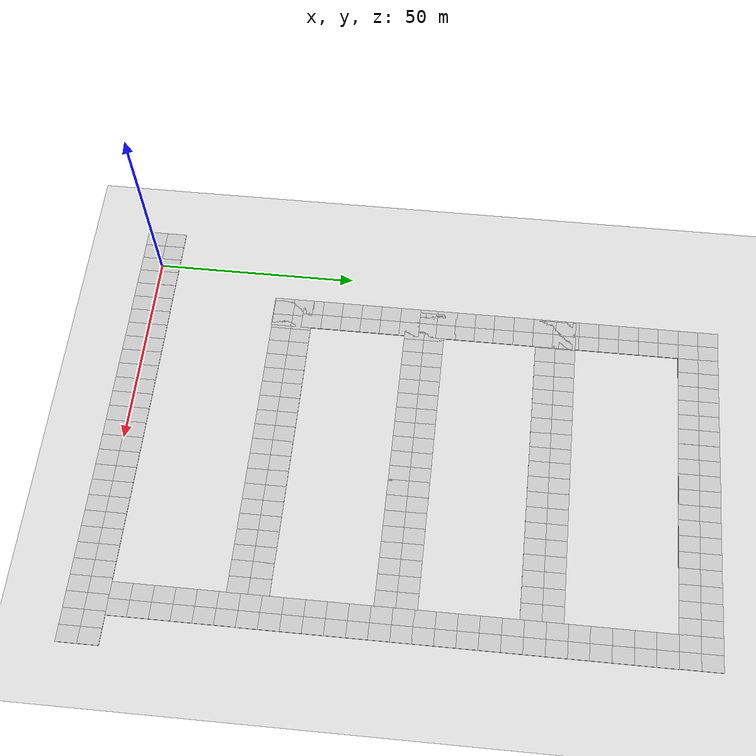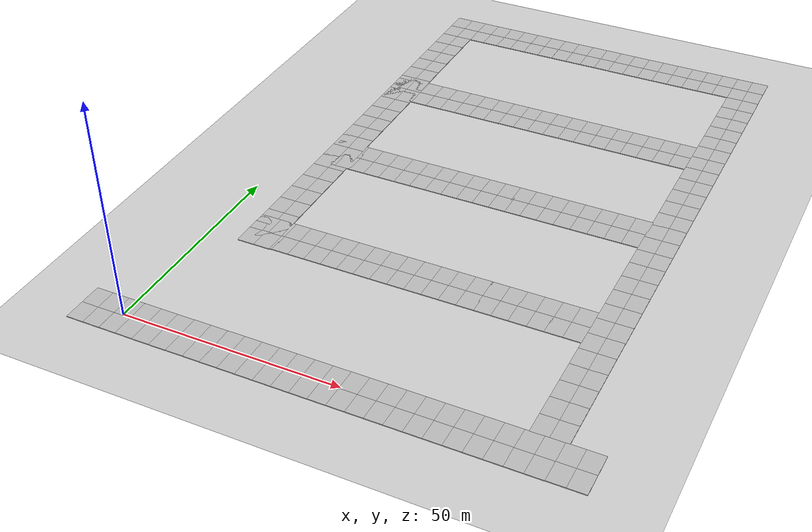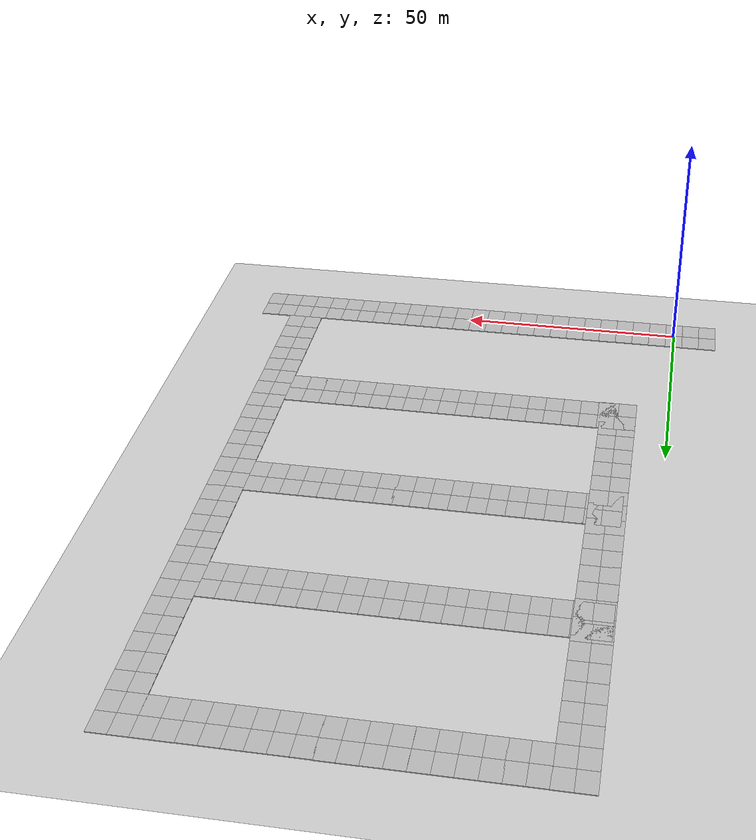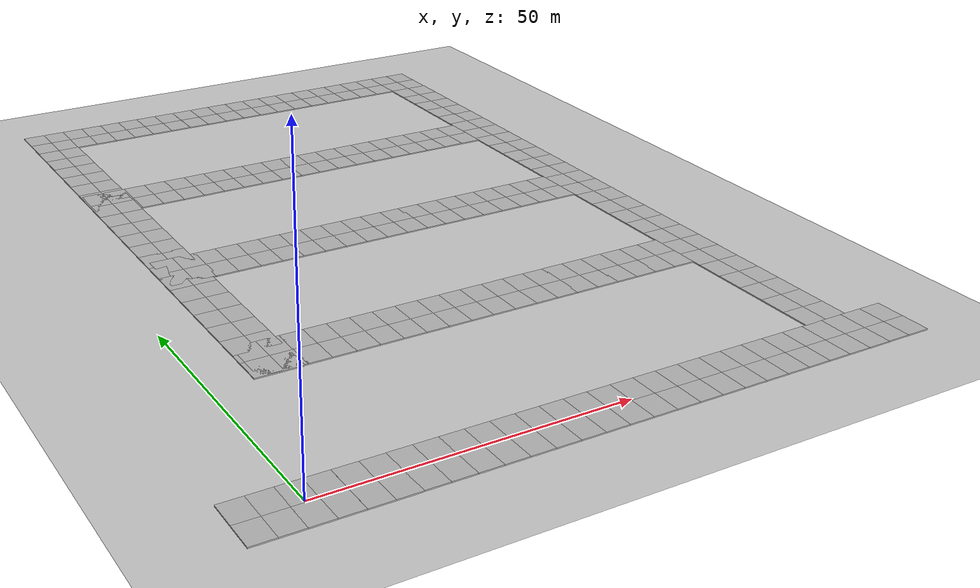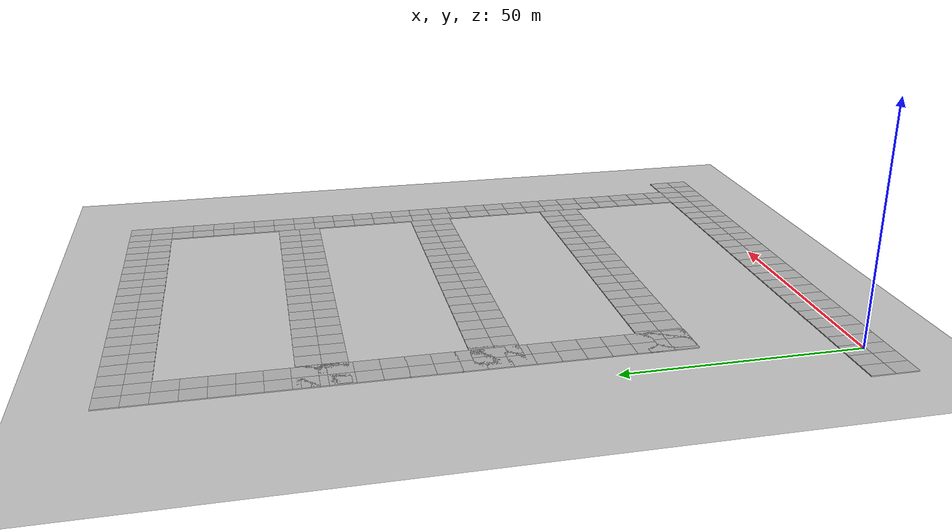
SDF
<sdf version="1.7">
 <world name="default">
  <light name="sun" type="directional">
   <pose>0 0 10 0 -0 0</pose>
   <diffuse>0.8 0.8 0.8 1</diffuse>
   <specular>0.2 0.2 0.2 1</specular>
   <attenuation>
    <range>1000</range>
    <constant>0.9</constant>
    <linear>0.01</linear>
    <quadratic>0.001</quadratic>
   </attenuation>
   <direction>-0.5 0.1 -0.9</direction>
   <spot><inner_angle>0</inner_angle><outer_angle>0</outer_angle><falloff>0</falloff></spot>
  </light>
  <model name="ground_plane">
   <static>1</static>
   <link name="link">
    <collision name="collision">
     <geometry><plane><normal>0 0 1</normal><size>100 100</size></plane></geometry>
     <surface>
      <contact><collide_bitmask>65535</collide_bitmask></contact>
      <friction><ode><mu>100</mu><mu2>50</mu2></ode></friction>
     </surface>
    </collision>
    <visual name="visual">
     <cast_shadows>0</cast_shadows>
     <geometry><plane><normal>0 0 1</normal><size>100 100</size></plane></geometry>
     <material>
      <script><uri>file://media/materials/scripts/gazebo.material</uri><name>Gazebo/Grey</name></script>
     </material>
    </visual>
   </link>
  </model>
  <gravity>0 0 -9.8</gravity>
  <magnetic_field>6e-06 2.3e-05 -4.2e-05</magnetic_field>
  <atmosphere type="adiabatic"/>
  <physics type="ode">
   <max_step_size>0.001</max_step_size>
   <real_time_factor>1</real_time_factor>
   <real_time_update_rate>1000</real_time_update_rate>
  </physics>
  <scene><ambient>0.4 0.4 0.4 1</ambient><background>0.7 0.7 0.7 1</background><shadows>1</shadows></scene>
  <spherical_coordinates>
   <surface_model>EARTH_WGS84</surface_model>
   <latitude_deg>0</latitude_deg>
   <longitude_deg>0</longitude_deg>
   <elevation>0</elevation>
   <heading_deg>0</heading_deg>
  </spherical_coordinates>
  <model name="mud_box">
   <static>1</static>
   <link name="link">
    <collision name="collision"><geometry><box><size>8 10 0.2</size></box></geometry></collision>
    <visual name="visual_1">
     <pose>-2 2.5 0 0 -0 0</pose>
     <cast_shadows>0</cast_shadows>
     <geometry><box><size>4 5 0.2</size></box></geometry>
     <material>
      <script>
       <uri>model://mud_box/materials/scripts</uri>
       <uri>model://mud_box/materials/textures</uri>
       <name>vrc/mud</name>
      </script>
     </material>
    </visual>
    <visual name="visual_2">
     <pose>2 2.5 0 0 -0 0</pose>
     <cast_shadows>0</cast_shadows>
     <geometry><box><size>4 5 0.2</size></box></geometry>
     <material>
      <script>
       <uri>model://mud_box/materials/scripts</uri>
       <uri>model://mud_box/materials/textures</uri>
       <name>vrc/mud</name>
      </script>
     </material>
    </visual>
    <visual name="visual_3">
     <pose>2 -2.5 0 0 -0 0</pose>
     <cast_shadows>0</cast_shadows>
     <geometry><box><size>4 5 0.2</size></box></geometry>
     <material>
      <script>
       <uri>model://mud_box/materials/scripts</uri>
       <uri>model://mud_box/materials/textures</uri>
       <name>vrc/mud</name>
      </script>
     </material>
    </visual>
    <visual name="visual_4">
     <pose>-2 -2.5 0 0 -0 0</pose>
     <cast_shadows>0</cast_shadows>
     <geometry><box><size>4 5 0.2</size></box></geometry>
     <material>
      <script>
       <uri>model://mud_box/materials/scripts</uri>
       <uri>model://mud_box/materials/textures</uri>
       <name>vrc/mud</name>
      </script>
     </material>
    </visual>
   </link>
   <pose>-6.0472 -0.38569 0 0 -0 0</pose>
  </model>
  <model name="mud_box_0">
   <static>1</static>
   <link name="link">
    <collision name="collision"><geometry><box><size>8 10 0.2</size></box></geometry></collision>
    <visual name="visual_1">
     <pose>-2 2.5 0 0 -0 0</pose>
     <cast_shadows>0</cast_shadows>
     <geometry><box><size>4 5 0.2</size></box></geometry>
     <material>
      <script>
       <uri>model://mud_box/materials/scripts</uri>
       <uri>model://mud_box/materials/textures</uri>
       <name>vrc/mud</name>
      </script>
     </material>
    </visual>
    <visual name="visual_2">
     <pose>2 2.5 0 0 -0 0</pose>
     <cast_shadows>0</cast_shadows>
     <geometry><box><size>4 5 0.2</size></box></geometry>
     <material>
      <script>
       <uri>model://mud_box/materials/scripts</uri>
       <uri>model://mud_box/materials/textures</uri>
       <name>vrc/mud</name>
      </script>
     </material>
    </visual>
    <visual name="visual_3">
     <pose>2 -2.5 0 0 -0 0</pose>
     <cast_shadows>0</cast_shadows>
     <geometry><box><size>4 5 0.2</size></box></geometry>
     <material>
      <script>
       <uri>model://mud_box/materials/scripts</uri>
       <uri>model://mud_box/materials/textures</uri>
       <name>vrc/mud</name>
      </script>
     </material>
    </visual>
    <visual name="visual_4">
     <pose>-2 -2.5 0 0 -0 0</pose>
     <cast_shadows>0</cast_shadows>
     <geometry><box><size>4 5 0.2</size></box></geometry>
     <material>
      <script>
       <uri>model://mud_box/materials/scripts</uri>
       <uri>model://mud_box/materials/textures</uri>
       <name>vrc/mud</name>
      </script>
     </material>
    </visual>
   </link>
   <pose>1.87582 -0.385693 0 0 -0 0</pose>
  </model>
  <model name="mud_box_clone">
   <static>1</static>
   <link name="link">
    <collision name="collision"><geometry><box><size>8 10 0.2</size></box></geometry></collision>
    <visual name="visual_1">
     <pose>-2 2.5 0 0 -0 0</pose>
     <cast_shadows>0</cast_shadows>
     <geometry><box><size>4 5 0.2</size></box></geometry>
     <material>
      <script>
       <uri>model://mud_box/materials/scripts</uri>
       <uri>model://mud_box/materials/textures</uri>
       <name>vrc/mud</name>
      </script>
     </material>
    </visual>
    <visual name="visual_2">
     <pose>2 2.5 0 0 -0 0</pose>
     <cast_shadows>0</cast_shadows>
     <geometry><box><size>4 5 0.2</size></box></geometry>
     <material>
      <script>
       <uri>model://mud_box/materials/scripts</uri>
       <uri>model://mud_box/materials/textures</uri>
       <name>vrc/mud</name>
      </script>
     </material>
    </visual>
    <visual name="visual_3">
     <pose>2 -2.5 0 0 -0 0</pose>
     <cast_shadows>0</cast_shadows>
     <geometry><box><size>4 5 0.2</size></box></geometry>
     <material>
      <script>
       <uri>model://mud_box/materials/scripts</uri>
       <uri>model://mud_box/materials/textures</uri>
       <name>vrc/mud</name>
      </script>
     </material>
    </visual>
    <visual name="visual_4">
     <pose>-2 -2.5 0 0 -0 0</pose>
     <cast_shadows>0</cast_shadows>
     <geometry><box><size>4 5 0.2</size></box></geometry>
     <material>
      <script>
       <uri>model://mud_box/materials/scripts</uri>
       <uri>model://mud_box/materials/textures</uri>
       <name>vrc/mud</name>
      </script>
     </material>
    </visual>
   </link>
   <pose>9.88835 -0.403056 0 0 -0 0</pose>
  </model>
  <model name="mud_box_1">
   <static>1</static>
   <link name="link">
    <collision name="collision"><geometry><box><size>8 10 0.2</size></box></geometry></collision>
    <visual name="visual_1">
     <pose>-2 2.5 0 0 -0 0</pose>
     <cast_shadows>0</cast_shadows>
     <geometry><box><size>4 5 0.2</size></box></geometry>
     <material>
      <script>
       <uri>model://mud_box/materials/scripts</uri>
       <uri>model://mud_box/materials/textures</uri>
       <name>vrc/mud</name>
      </script>
     </material>
    </visual>
    <visual name="visual_2">
     <pose>2 2.5 0 0 -0 0</pose>
     <cast_shadows>0</cast_shadows>
     <geometry><box><size>4 5 0.2</size></box></geometry>
     <material>
      <script>
       <uri>model://mud_box/materials/scripts</uri>
       <uri>model://mud_box/materials/textures</uri>
       <name>vrc/mud</name>
      </script>
     </material>
    </visual>
    <visual name="visual_3">
     <pose>2 -2.5 0 0 -0 0</pose>
     <cast_shadows>0</cast_shadows>
     <geometry><box><size>4 5 0.2</size></box></geometry>
     <material>
      <script>
       <uri>model://mud_box/materials/scripts</uri>
       <uri>model://mud_box/materials/textures</uri>
       <name>vrc/mud</name>
      </script>
     </material>
    </visual>
    <visual name="visual_4">
     <pose>-2 -2.5 0 0 -0 0</pose>
     <cast_shadows>0</cast_shadows>
     <geometry><box><size>4 5 0.2</size></box></geometry>
     <material>
      <script>
       <uri>model://mud_box/materials/scripts</uri>
       <uri>model://mud_box/materials/textures</uri>
       <name>vrc/mud</name>
      </script>
     </material>
    </visual>
   </link>
   <pose>17.8296 -0.357157 0 0 -0 0</pose>
  </model>
  <model name="mud_box_2">
   <static>1</static>
   <link name="link">
    <collision name="collision"><geometry><box><size>8 10 0.2</size></box></geometry></collision>
    <visual name="visual_1">
     <pose>-2 2.5 0 0 -0 0</pose>
     <cast_shadows>0</cast_shadows>
     <geometry><box><size>4 5 0.2</size></box></geometry>
     <material>
      <script>
       <uri>model://mud_box/materials/scripts</uri>
       <uri>model://mud_box/materials/textures</uri>
       <name>vrc/mud</name>
      </script>
     </material>
    </visual>
    <visual name="visual_2">
     <pose>2 2.5 0 0 -0 0</pose>
     <cast_shadows>0</cast_shadows>
     <geometry><box><size>4 5 0.2</size></box></geometry>
     <material>
      <script>
       <uri>model://mud_box/materials/scripts</uri>
       <uri>model://mud_box/materials/textures</uri>
       <name>vrc/mud</name>
      </script>
     </material>
    </visual>
    <visual name="visual_3">
     <pose>2 -2.5 0 0 -0 0</pose>
     <cast_shadows>0</cast_shadows>
     <geometry><box><size>4 5 0.2</size></box></geometry>
     <material>
      <script>
       <uri>model://mud_box/materials/scripts</uri>
       <uri>model://mud_box/materials/textures</uri>
       <name>vrc/mud</name>
      </script>
     </material>
    </visual>
    <visual name="visual_4">
     <pose>-2 -2.5 0 0 -0 0</pose>
     <cast_shadows>0</cast_shadows>
     <geometry><box><size>4 5 0.2</size></box></geometry>
     <material>
      <script>
       <uri>model://mud_box/materials/scripts</uri>
       <uri>model://mud_box/materials/textures</uri>
       <name>vrc/mud</name>
      </script>
     </material>
    </visual>
   </link>
   <pose>25.7709 -0.35716 0 0 -0 0</pose>
  </model>
  <model name="mud_box_3">
   <static>1</static>
   <link name="link">
    <collision name="collision"><geometry><box><size>8 10 0.2</size></box></geometry></collision>
    <visual name="visual_1">
     <pose>-2 2.5 0 0 -0 0</pose>
     <cast_shadows>0</cast_shadows>
     <geometry><box><size>4 5 0.2</size></box></geometry>
     <material>
      <script>
       <uri>model://mud_box/materials/scripts</uri>
       <uri>model://mud_box/materials/textures</uri>
       <name>vrc/mud</name>
      </script>
     </material>
    </visual>
    <visual name="visual_2">
     <pose>2 2.5 0 0 -0 0</pose>
     <cast_shadows>0</cast_shadows>
     <geometry><box><size>4 5 0.2</size></box></geometry>
     <material>
      <script>
       <uri>model://mud_box/materials/scripts</uri>
       <uri>model://mud_box/materials/textures</uri>
       <name>vrc/mud</name>
      </script>
     </material>
    </visual>
    <visual name="visual_3">
     <pose>2 -2.5 0 0 -0 0</pose>
     <cast_shadows>0</cast_shadows>
     <geometry><box><size>4 5 0.2</size></box></geometry>
     <material>
      <script>
       <uri>model://mud_box/materials/scripts</uri>
       <uri>model://mud_box/materials/textures</uri>
       <name>vrc/mud</name>
      </script>
     </material>
    </visual>
    <visual name="visual_4">
     <pose>-2 -2.5 0 0 -0 0</pose>
     <cast_shadows>0</cast_shadows>
     <geometry><box><size>4 5 0.2</size></box></geometry>
     <material>
      <script>
       <uri>model://mud_box/materials/scripts</uri>
       <uri>model://mud_box/materials/textures</uri>
       <name>vrc/mud</name>
      </script>
     </material>
    </visual>
   </link>
   <pose>33.7582 -0.357154 0 0 -0 0</pose>
  </model>
  <model name="mud_box_4">
   <static>1</static>
   <link name="link">
    <collision name="collision"><geometry><box><size>8 10 0.2</size></box></geometry></collision>
    <visual name="visual_1">
     <pose>-2 2.5 0 0 -0 0</pose>
     <cast_shadows>0</cast_shadows>
     <geometry><box><size>4 5 0.2</size></box></geometry>
     <material>
      <script>
       <uri>model://mud_box/materials/scripts</uri>
       <uri>model://mud_box/materials/textures</uri>
       <name>vrc/mud</name>
      </script>
     </material>
    </visual>
    <visual name="visual_2">
     <pose>2 2.5 0 0 -0 0</pose>
     <cast_shadows>0</cast_shadows>
     <geometry><box><size>4 5 0.2</size></box></geometry>
     <material>
      <script>
       <uri>model://mud_box/materials/scripts</uri>
       <uri>model://mud_box/materials/textures</uri>
       <name>vrc/mud</name>
      </script>
     </material>
    </visual>
    <visual name="visual_3">
     <pose>2 -2.5 0 0 -0 0</pose>
     <cast_shadows>0</cast_shadows>
     <geometry><box><size>4 5 0.2</size></box></geometry>
     <material>
      <script>
       <uri>model://mud_box/materials/scripts</uri>
       <uri>model://mud_box/materials/textures</uri>
       <name>vrc/mud</name>
      </script>
     </material>
    </visual>
    <visual name="visual_4">
     <pose>-2 -2.5 0 0 -0 0</pose>
     <cast_shadows>0</cast_shadows>
     <geometry><box><size>4 5 0.2</size></box></geometry>
     <material>
      <script>
       <uri>model://mud_box/materials/scripts</uri>
       <uri>model://mud_box/materials/textures</uri>
       <name>vrc/mud</name>
      </script>
     </material>
    </visual>
   </link>
   <pose>41.7454 -0.357152 0 0 -0 0</pose>
  </model>
  <model name="mud_box_5">
   <static>1</static>
   <link name="link">
    <collision name="collision"><geometry><box><size>8 10 0.2</size></box></geometry></collision>
    <visual name="visual_1">
     <pose>-2 2.5 0 0 -0 0</pose>
     <cast_shadows>0</cast_shadows>
     <geometry><box><size>4 5 0.2</size></box></geometry>
     <material>
      <script>
       <uri>model://mud_box/materials/scripts</uri>
       <uri>model://mud_box/materials/textures</uri>
       <name>vrc/mud</name>
      </script>
     </material>
    </visual>
    <visual name="visual_2">
     <pose>2 2.5 0 0 -0 0</pose>
     <cast_shadows>0</cast_shadows>
     <geometry><box><size>4 5 0.2</size></box></geometry>
     <material>
      <script>
       <uri>model://mud_box/materials/scripts</uri>
       <uri>model://mud_box/materials/textures</uri>
       <name>vrc/mud</name>
      </script>
     </material>
    </visual>
    <visual name="visual_3">
     <pose>2 -2.5 0 0 -0 0</pose>
     <cast_shadows>0</cast_shadows>
     <geometry><box><size>4 5 0.2</size></box></geometry>
     <material>
      <script>
       <uri>model://mud_box/materials/scripts</uri>
       <uri>model://mud_box/materials/textures</uri>
       <name>vrc/mud</name>
      </script>
     </material>
    </visual>
    <visual name="visual_4">
     <pose>-2 -2.5 0 0 -0 0</pose>
     <cast_shadows>0</cast_shadows>
     <geometry><box><size>4 5 0.2</size></box></geometry>
     <material>
      <script>
       <uri>model://mud_box/materials/scripts</uri>
       <uri>model://mud_box/materials/textures</uri>
       <name>vrc/mud</name>
      </script>
     </material>
    </visual>
   </link>
   <pose>49.7326 -0.357155 0 0 -0 0</pose>
  </model>
  <model name="mud_box_6">
   <static>1</static>
   <link name="link">
    <collision name="collision"><geometry><box><size>8 10 0.2</size></box></geometry></collision>
    <visual name="visual_1">
     <pose>-2 2.5 0 0 -0 0</pose>
     <cast_shadows>0</cast_shadows>
     <geometry><box><size>4 5 0.2</size></box></geometry>
     <material>
      <script>
       <uri>model://mud_box/materials/scripts</uri>
       <uri>model://mud_box/materials/textures</uri>
       <name>vrc/mud</name>
      </script>
     </material>
    </visual>
    <visual name="visual_2">
     <pose>2 2.5 0 0 -0 0</pose>
     <cast_shadows>0</cast_shadows>
     <geometry><box><size>4 5 0.2</size></box></geometry>
     <material>
      <script>
       <uri>model://mud_box/materials/scripts</uri>
       <uri>model://mud_box/materials/textures</uri>
       <name>vrc/mud</name>
      </script>
     </material>
    </visual>
    <visual name="visual_3">
     <pose>2 -2.5 0 0 -0 0</pose>
     <cast_shadows>0</cast_shadows>
     <geometry><box><size>4 5 0.2</size></box></geometry>
     <material>
      <script>
       <uri>model://mud_box/materials/scripts</uri>
       <uri>model://mud_box/materials/textures</uri>
       <name>vrc/mud</name>
      </script>
     </material>
    </visual>
    <visual name="visual_4">
     <pose>-2 -2.5 0 0 -0 0</pose>
     <cast_shadows>0</cast_shadows>
     <geometry><box><size>4 5 0.2</size></box></geometry>
     <material>
      <script>
       <uri>model://mud_box/materials/scripts</uri>
       <uri>model://mud_box/materials/textures</uri>
       <name>vrc/mud</name>
      </script>
     </material>
    </visual>
   </link>
   <pose>57.7198 -0.357153 0 0 -0 0</pose>
  </model>
  <model name="mud_box_7">
   <static>1</static>
   <link name="link">
    <collision name="collision"><geometry><box><size>8 10 0.2</size></box></geometry></collision>
    <visual name="visual_1">
     <pose>-2 2.5 0 0 -0 0</pose>
     <cast_shadows>0</cast_shadows>
     <geometry><box><size>4 5 0.2</size></box></geometry>
     <material>
      <script>
       <uri>model://mud_box/materials/scripts</uri>
       <uri>model://mud_box/materials/textures</uri>
       <name>vrc/mud</name>
      </script>
     </material>
    </visual>
    <visual name="visual_2">
     <pose>2 2.5 0 0 -0 0</pose>
     <cast_shadows>0</cast_shadows>
     <geometry><box><size>4 5 0.2</size></box></geometry>
     <material>
      <script>
       <uri>model://mud_box/materials/scripts</uri>
       <uri>model://mud_box/materials/textures</uri>
       <name>vrc/mud</name>
      </script>
     </material>
    </visual>
    <visual name="visual_3">
     <pose>2 -2.5 0 0 -0 0</pose>
     <cast_shadows>0</cast_shadows>
     <geometry><box><size>4 5 0.2</size></box></geometry>
     <material>
      <script>
       <uri>model://mud_box/materials/scripts</uri>
       <uri>model://mud_box/materials/textures</uri>
       <name>vrc/mud</name>
      </script>
     </material>
    </visual>
    <visual name="visual_4">
     <pose>-2 -2.5 0 0 -0 0</pose>
     <cast_shadows>0</cast_shadows>
     <geometry><box><size>4 5 0.2</size></box></geometry>
     <material>
      <script>
       <uri>model://mud_box/materials/scripts</uri>
       <uri>model://mud_box/materials/textures</uri>
       <name>vrc/mud</name>
      </script>
     </material>
    </visual>
   </link>
   <pose>65.707 -0.357156 0 0 -0 0</pose>
  </model>
  <model name="mud_box_8">
   <static>1</static>
   <link name="link">
    <collision name="collision"><geometry><box><size>8 10 0.2</size></box></geometry></collision>
    <visual name="visual_1">
     <pose>-2 2.5 0 0 -0 0</pose>
     <cast_shadows>0</cast_shadows>
     <geometry><box><size>4 5 0.2</size></box></geometry>
     <material>
      <script>
       <uri>model://mud_box/materials/scripts</uri>
       <uri>model://mud_box/materials/textures</uri>
       <name>vrc/mud</name>
      </script>
     </material>
    </visual>
    <visual name="visual_2">
     <pose>2 2.5 0 0 -0 0</pose>
     <cast_shadows>0</cast_shadows>
     <geometry><box><size>4 5 0.2</size></box></geometry>
     <material>
      <script>
       <uri>model://mud_box/materials/scripts</uri>
       <uri>model://mud_box/materials/textures</uri>
       <name>vrc/mud</name>
      </script>
     </material>
    </visual>
    <visual name="visual_3">
     <pose>2 -2.5 0 0 -0 0</pose>
     <cast_shadows>0</cast_shadows>
     <geometry><box><size>4 5 0.2</size></box></geometry>
     <material>
      <script>
       <uri>model://mud_box/materials/scripts</uri>
       <uri>model://mud_box/materials/textures</uri>
       <name>vrc/mud</name>
      </script>
     </material>
    </visual>
    <visual name="visual_4">
     <pose>-2 -2.5 0 0 -0 0</pose>
     <cast_shadows>0</cast_shadows>
     <geometry><box><size>4 5 0.2</size></box></geometry>
     <material>
      <script>
       <uri>model://mud_box/materials/scripts</uri>
       <uri>model://mud_box/materials/textures</uri>
       <name>vrc/mud</name>
      </script>
     </material>
    </visual>
   </link>
   <pose>73.6942 -0.357155 0 0 -0 0</pose>
  </model>
  <model name="mud_box_9">
   <static>1</static>
   <link name="link">
    <collision name="collision"><geometry><box><size>8 10 0.2</size></box></geometry></collision>
    <visual name="visual_1">
     <pose>-2 2.5 0 0 -0 0</pose>
     <cast_shadows>0</cast_shadows>
     <geometry><box><size>4 5 0.2</size></box></geometry>
     <material>
      <script>
       <uri>model://mud_box/materials/scripts</uri>
       <uri>model://mud_box/materials/textures</uri>
       <name>vrc/mud</name>
      </script>
     </material>
    </visual>
    <visual name="visual_2">
     <pose>2 2.5 0 0 -0 0</pose>
     <cast_shadows>0</cast_shadows>
     <geometry><box><size>4 5 0.2</size></box></geometry>
     <material>
      <script>
       <uri>model://mud_box/materials/scripts</uri>
       <uri>model://mud_box/materials/textures</uri>
       <name>vrc/mud</name>
      </script>
     </material>
    </visual>
    <visual name="visual_3">
     <pose>2 -2.5 0 0 -0 0</pose>
     <cast_shadows>0</cast_shadows>
     <geometry><box><size>4 5 0.2</size></box></geometry>
     <material>
      <script>
       <uri>model://mud_box/materials/scripts</uri>
       <uri>model://mud_box/materials/textures</uri>
       <name>vrc/mud</name>
      </script>
     </material>
    </visual>
    <visual name="visual_4">
     <pose>-2 -2.5 0 0 -0 0</pose>
     <cast_shadows>0</cast_shadows>
     <geometry><box><size>4 5 0.2</size></box></geometry>
     <material>
      <script>
       <uri>model://mud_box/materials/scripts</uri>
       <uri>model://mud_box/materials/textures</uri>
       <name>vrc/mud</name>
      </script>
     </material>
    </visual>
   </link>
   <pose>81.6814 -0.357154 0 0 -0 0</pose>
  </model>
  <model name="mud_box_10">
   <static>1</static>
   <link name="link">
    <collision name="collision"><geometry><box><size>8 10 0.2</size></box></geometry></collision>
    <visual name="visual_1">
     <pose>-2 2.5 0 0 -0 0</pose>
     <cast_shadows>0</cast_shadows>
     <geometry><box><size>4 5 0.2</size></box></geometry>
     <material>
      <script>
       <uri>model://mud_box/materials/scripts</uri>
       <uri>model://mud_box/materials/textures</uri>
       <name>vrc/mud</name>
      </script>
     </material>
    </visual>
    <visual name="visual_2">
     <pose>2 2.5 0 0 -0 0</pose>
     <cast_shadows>0</cast_shadows>
     <geometry><box><size>4 5 0.2</size></box></geometry>
     <material>
      <script>
       <uri>model://mud_box/materials/scripts</uri>
       <uri>model://mud_box/materials/textures</uri>
       <name>vrc/mud</name>
      </script>
     </material>
    </visual>
    <visual name="visual_3">
     <pose>2 -2.5 0 0 -0 0</pose>
     <cast_shadows>0</cast_shadows>
     <geometry><box><size>4 5 0.2</size></box></geometry>
     <material>
      <script>
       <uri>model://mud_box/materials/scripts</uri>
       <uri>model://mud_box/materials/textures</uri>
       <name>vrc/mud</name>
      </script>
     </material>
    </visual>
    <visual name="visual_4">
     <pose>-2 -2.5 0 0 -0 0</pose>
     <cast_shadows>0</cast_shadows>
     <geometry><box><size>4 5 0.2</size></box></geometry>
     <material>
      <script>
       <uri>model://mud_box/materials/scripts</uri>
       <uri>model://mud_box/materials/textures</uri>
       <name>vrc/mud</name>
      </script>
     </material>
    </visual>
   </link>
   <pose>89.6227 -0.357157 0 0 -0 0</pose>
  </model>
  <model name="mud_box_11">
   <static>1</static>
   <link name="link">
    <collision name="collision"><geometry><box><size>8 10 0.2</size></box></geometry></collision>
    <visual name="visual_1">
     <pose>-2 2.5 0 0 -0 0</pose>
     <cast_shadows>0</cast_shadows>
     <geometry><box><size>4 5 0.2</size></box></geometry>
     <material>
      <script>
       <uri>model://mud_box/materials/scripts</uri>
       <uri>model://mud_box/materials/textures</uri>
       <name>vrc/mud</name>
      </script>
     </material>
    </visual>
    <visual name="visual_2">
     <pose>2 2.5 0 0 -0 0</pose>
     <cast_shadows>0</cast_shadows>
     <geometry><box><size>4 5 0.2</size></box></geometry>
     <material>
      <script>
       <uri>model://mud_box/materials/scripts</uri>
       <uri>model://mud_box/materials/textures</uri>
       <name>vrc/mud</name>
      </script>
     </material>
    </visual>
    <visual name="visual_3">
     <pose>2 -2.5 0 0 -0 0</pose>
     <cast_shadows>0</cast_shadows>
     <geometry><box><size>4 5 0.2</size></box></geometry>
     <material>
      <script>
       <uri>model://mud_box/materials/scripts</uri>
       <uri>model://mud_box/materials/textures</uri>
       <name>vrc/mud</name>
      </script>
     </material>
    </visual>
    <visual name="visual_4">
     <pose>-2 -2.5 0 0 -0 0</pose>
     <cast_shadows>0</cast_shadows>
     <geometry><box><size>4 5 0.2</size></box></geometry>
     <material>
      <script>
       <uri>model://mud_box/materials/scripts</uri>
       <uri>model://mud_box/materials/textures</uri>
       <name>vrc/mud</name>
      </script>
     </material>
    </visual>
   </link>
   <pose>97.6099 -0.311259 0 0 -0 0</pose>
  </model>
  <model name="mud_box_12">
   <static>1</static>
   <link name="link">
    <collision name="collision"><geometry><box><size>8 10 0.2</size></box></geometry></collision>
    <visual name="visual_1">
     <pose>-2 2.5 0 0 -0 0</pose>
     <cast_shadows>0</cast_shadows>
     <geometry><box><size>4 5 0.2</size></box></geometry>
     <material>
      <script>
       <uri>model://mud_box/materials/scripts</uri>
       <uri>model://mud_box/materials/textures</uri>
       <name>vrc/mud</name>
      </script>
     </material>
    </visual>
    <visual name="visual_2">
     <pose>2 2.5 0 0 -0 0</pose>
     <cast_shadows>0</cast_shadows>
     <geometry><box><size>4 5 0.2</size></box></geometry>
     <material>
      <script>
       <uri>model://mud_box/materials/scripts</uri>
       <uri>model://mud_box/materials/textures</uri>
       <name>vrc/mud</name>
      </script>
     </material>
    </visual>
    <visual name="visual_3">
     <pose>2 -2.5 0 0 -0 0</pose>
     <cast_shadows>0</cast_shadows>
     <geometry><box><size>4 5 0.2</size></box></geometry>
     <material>
      <script>
       <uri>model://mud_box/materials/scripts</uri>
       <uri>model://mud_box/materials/textures</uri>
       <name>vrc/mud</name>
      </script>
     </material>
    </visual>
    <visual name="visual_4">
     <pose>-2 -2.5 0 0 -0 0</pose>
     <cast_shadows>0</cast_shadows>
     <geometry><box><size>4 5 0.2</size></box></geometry>
     <material>
      <script>
       <uri>model://mud_box/materials/scripts</uri>
       <uri>model://mud_box/materials/textures</uri>
       <name>vrc/mud</name>
      </script>
     </material>
    </visual>
   </link>
   <pose>90.4949 9.55798 0 0 -0 0</pose>
  </model>
  <model name="mud_box_13">
   <static>1</static>
   <link name="link">
    <collision name="collision"><geometry><box><size>8 10 0.2</size></box></geometry></collision>
    <visual name="visual_1">
     <pose>-2 2.5 0 0 -0 0</pose>
     <cast_shadows>0</cast_shadows>
     <geometry><box><size>4 5 0.2</size></box></geometry>
     <material>
      <script>
       <uri>model://mud_box/materials/scripts</uri>
       <uri>model://mud_box/materials/textures</uri>
       <name>vrc/mud</name>
      </script>
     </material>
    </visual>
    <visual name="visual_2">
     <pose>2 2.5 0 0 -0 0</pose>
     <cast_shadows>0</cast_shadows>
     <geometry><box><size>4 5 0.2</size></box></geometry>
     <material>
      <script>
       <uri>model://mud_box/materials/scripts</uri>
       <uri>model://mud_box/materials/textures</uri>
       <name>vrc/mud</name>
      </script>
     </material>
    </visual>
    <visual name="visual_3">
     <pose>2 -2.5 0 0 -0 0</pose>
     <cast_shadows>0</cast_shadows>
     <geometry><box><size>4 5 0.2</size></box></geometry>
     <material>
      <script>
       <uri>model://mud_box/materials/scripts</uri>
       <uri>model://mud_box/materials/textures</uri>
       <name>vrc/mud</name>
      </script>
     </material>
    </visual>
    <visual name="visual_4">
     <pose>-2 -2.5 0 0 -0 0</pose>
     <cast_shadows>0</cast_shadows>
     <geometry><box><size>4 5 0.2</size></box></geometry>
     <material>
      <script>
       <uri>model://mud_box/materials/scripts</uri>
       <uri>model://mud_box/materials/textures</uri>
       <name>vrc/mud</name>
      </script>
     </material>
    </visual>
   </link>
   <pose>90.4949 19.519 0 0 -0 0</pose>
  </model>
  <model name="mud_box_14">
   <static>1</static>
   <link name="link">
    <collision name="collision"><geometry><box><size>8 10 0.2</size></box></geometry></collision>
    <visual name="visual_1">
     <pose>-2 2.5 0 0 -0 0</pose>
     <cast_shadows>0</cast_shadows>
     <geometry><box><size>4 5 0.2</size></box></geometry>
     <material>
      <script>
       <uri>model://mud_box/materials/scripts</uri>
       <uri>model://mud_box/materials/textures</uri>
       <name>vrc/mud</name>
      </script>
     </material>
    </visual>
    <visual name="visual_2">
     <pose>2 2.5 0 0 -0 0</pose>
     <cast_shadows>0</cast_shadows>
     <geometry><box><size>4 5 0.2</size></box></geometry>
     <material>
      <script>
       <uri>model://mud_box/materials/scripts</uri>
       <uri>model://mud_box/materials/textures</uri>
       <name>vrc/mud</name>
      </script>
     </material>
    </visual>
    <visual name="visual_3">
     <pose>2 -2.5 0 0 -0 0</pose>
     <cast_shadows>0</cast_shadows>
     <geometry><box><size>4 5 0.2</size></box></geometry>
     <material>
      <script>
       <uri>model://mud_box/materials/scripts</uri>
       <uri>model://mud_box/materials/textures</uri>
       <name>vrc/mud</name>
      </script>
     </material>
    </visual>
    <visual name="visual_4">
     <pose>-2 -2.5 0 0 -0 0</pose>
     <cast_shadows>0</cast_shadows>
     <geometry><box><size>4 5 0.2</size></box></geometry>
     <material>
      <script>
       <uri>model://mud_box/materials/scripts</uri>
       <uri>model://mud_box/materials/textures</uri>
       <name>vrc/mud</name>
      </script>
     </material>
    </visual>
   </link>
   <pose>90.4925 29.4514 0 0 -0 0</pose>
  </model>
  <model name="mud_box_15">
   <static>1</static>
   <link name="link">
    <collision name="collision"><geometry><box><size>8 10 0.2</size></box></geometry></collision>
    <visual name="visual_1">
     <pose>-2 2.5 0 0 -0 0</pose>
     <cast_shadows>0</cast_shadows>
     <geometry><box><size>4 5 0.2</size></box></geometry>
     <material>
      <script>
       <uri>model://mud_box/materials/scripts</uri>
       <uri>model://mud_box/materials/textures</uri>
       <name>vrc/mud</name>
      </script>
     </material>
    </visual>
    <visual name="visual_2">
     <pose>2 2.5 0 0 -0 0</pose>
     <cast_shadows>0</cast_shadows>
     <geometry><box><size>4 5 0.2</size></box></geometry>
     <material>
      <script>
       <uri>model://mud_box/materials/scripts</uri>
       <uri>model://mud_box/materials/textures</uri>
       <name>vrc/mud</name>
      </script>
     </material>
    </visual>
    <visual name="visual_3">
     <pose>2 -2.5 0 0 -0 0</pose>
     <cast_shadows>0</cast_shadows>
     <geometry><box><size>4 5 0.2</size></box></geometry>
     <material>
      <script>
       <uri>model://mud_box/materials/scripts</uri>
       <uri>model://mud_box/materials/textures</uri>
       <name>vrc/mud</name>
      </script>
     </material>
    </visual>
    <visual name="visual_4">
     <pose>-2 -2.5 0 0 -0 0</pose>
     <cast_shadows>0</cast_shadows>
     <geometry><box><size>4 5 0.2</size></box></geometry>
     <material>
      <script>
       <uri>model://mud_box/materials/scripts</uri>
       <uri>model://mud_box/materials/textures</uri>
       <name>vrc/mud</name>
      </script>
     </material>
    </visual>
   </link>
   <pose>90.5332 39.4327 0 0 -0 0</pose>
  </model>
  <model name="mud_box_16">
   <static>1</static>
   <link name="link">
    <collision name="collision"><geometry><box><size>8 10 0.2</size></box></geometry></collision>
    <visual name="visual_1">
     <pose>-2 2.5 0 0 -0 0</pose>
     <cast_shadows>0</cast_shadows>
     <geometry><box><size>4 5 0.2</size></box></geometry>
     <material>
      <script>
       <uri>model://mud_box/materials/scripts</uri>
       <uri>model://mud_box/materials/textures</uri>
       <name>vrc/mud</name>
      </script>
     </material>
    </visual>
    <visual name="visual_2">
     <pose>2 2.5 0 0 -0 0</pose>
     <cast_shadows>0</cast_shadows>
     <geometry><box><size>4 5 0.2</size></box></geometry>
     <material>
      <script>
       <uri>model://mud_box/materials/scripts</uri>
       <uri>model://mud_box/materials/textures</uri>
       <name>vrc/mud</name>
      </script>
     </material>
    </visual>
    <visual name="visual_3">
     <pose>2 -2.5 0 0 -0 0</pose>
     <cast_shadows>0</cast_shadows>
     <geometry><box><size>4 5 0.2</size></box></geometry>
     <material>
      <script>
       <uri>model://mud_box/materials/scripts</uri>
       <uri>model://mud_box/materials/textures</uri>
       <name>vrc/mud</name>
      </script>
     </material>
    </visual>
    <visual name="visual_4">
     <pose>-2 -2.5 0 0 -0 0</pose>
     <cast_shadows>0</cast_shadows>
     <geometry><box><size>4 5 0.2</size></box></geometry>
     <material>
      <script>
       <uri>model://mud_box/materials/scripts</uri>
       <uri>model://mud_box/materials/textures</uri>
       <name>vrc/mud</name>
      </script>
     </material>
    </visual>
   </link>
   <pose>90.5332 49.4199 0 0 -0 0</pose>
  </model>
  <model name="mud_box_17">
   <static>1</static>
   <link name="link">
    <collision name="collision"><geometry><box><size>8 10 0.2</size></box></geometry></collision>
    <visual name="visual_1">
     <pose>-2 2.5 0 0 -0 0</pose>
     <cast_shadows>0</cast_shadows>
     <geometry><box><size>4 5 0.2</size></box></geometry>
     <material>
      <script>
       <uri>model://mud_box/materials/scripts</uri>
       <uri>model://mud_box/materials/textures</uri>
       <name>vrc/mud</name>
      </script>
     </material>
    </visual>
    <visual name="visual_2">
     <pose>2 2.5 0 0 -0 0</pose>
     <cast_shadows>0</cast_shadows>
     <geometry><box><size>4 5 0.2</size></box></geometry>
     <material>
      <script>
       <uri>model://mud_box/materials/scripts</uri>
       <uri>model://mud_box/materials/textures</uri>
       <name>vrc/mud</name>
      </script>
     </material>
    </visual>
    <visual name="visual_3">
     <pose>2 -2.5 0 0 -0 0</pose>
     <cast_shadows>0</cast_shadows>
     <geometry><box><size>4 5 0.2</size></box></geometry>
     <material>
      <script>
       <uri>model://mud_box/materials/scripts</uri>
       <uri>model://mud_box/materials/textures</uri>
       <name>vrc/mud</name>
      </script>
     </material>
    </visual>
    <visual name="visual_4">
     <pose>-2 -2.5 0 0 -0 0</pose>
     <cast_shadows>0</cast_shadows>
     <geometry><box><size>4 5 0.2</size></box></geometry>
     <material>
      <script>
       <uri>model://mud_box/materials/scripts</uri>
       <uri>model://mud_box/materials/textures</uri>
       <name>vrc/mud</name>
      </script>
     </material>
    </visual>
   </link>
   <pose>90.5332 59.407 0 0 -0 0</pose>
  </model>
  <model name="mud_box_18">
   <static>1</static>
   <link name="link">
    <collision name="collision"><geometry><box><size>8 10 0.2</size></box></geometry></collision>
    <visual name="visual_1">
     <pose>-2 2.5 0 0 -0 0</pose>
     <cast_shadows>0</cast_shadows>
     <geometry><box><size>4 5 0.2</size></box></geometry>
     <material>
      <script>
       <uri>model://mud_box/materials/scripts</uri>
       <uri>model://mud_box/materials/textures</uri>
       <name>vrc/mud</name>
      </script>
     </material>
    </visual>
    <visual name="visual_2">
     <pose>2 2.5 0 0 -0 0</pose>
     <cast_shadows>0</cast_shadows>
     <geometry><box><size>4 5 0.2</size></box></geometry>
     <material>
      <script>
       <uri>model://mud_box/materials/scripts</uri>
       <uri>model://mud_box/materials/textures</uri>
       <name>vrc/mud</name>
      </script>
     </material>
    </visual>
    <visual name="visual_3">
     <pose>2 -2.5 0 0 -0 0</pose>
     <cast_shadows>0</cast_shadows>
     <geometry><box><size>4 5 0.2</size></box></geometry>
     <material>
      <script>
       <uri>model://mud_box/materials/scripts</uri>
       <uri>model://mud_box/materials/textures</uri>
       <name>vrc/mud</name>
      </script>
     </material>
    </visual>
    <visual name="visual_4">
     <pose>-2 -2.5 0 0 -0 0</pose>
     <cast_shadows>0</cast_shadows>
     <geometry><box><size>4 5 0.2</size></box></geometry>
     <material>
      <script>
       <uri>model://mud_box/materials/scripts</uri>
       <uri>model://mud_box/materials/textures</uri>
       <name>vrc/mud</name>
      </script>
     </material>
    </visual>
   </link>
   <pose>90.5332 69.3941 0 0 -0 0</pose>
  </model>
  <model name="mud_box_19">
   <static>1</static>
   <link name="link">
    <collision name="collision"><geometry><box><size>8 10 0.2</size></box></geometry></collision>
    <visual name="visual_1">
     <pose>-2 2.5 0 0 -0 0</pose>
     <cast_shadows>0</cast_shadows>
     <geometry><box><size>4 5 0.2</size></box></geometry>
     <material>
      <script>
       <uri>model://mud_box/materials/scripts</uri>
       <uri>model://mud_box/materials/textures</uri>
       <name>vrc/mud</name>
      </script>
     </material>
    </visual>
    <visual name="visual_2">
     <pose>2 2.5 0 0 -0 0</pose>
     <cast_shadows>0</cast_shadows>
     <geometry><box><size>4 5 0.2</size></box></geometry>
     <material>
      <script>
       <uri>model://mud_box/materials/scripts</uri>
       <uri>model://mud_box/materials/textures</uri>
       <name>vrc/mud</name>
      </script>
     </material>
    </visual>
    <visual name="visual_3">
     <pose>2 -2.5 0 0 -0 0</pose>
     <cast_shadows>0</cast_shadows>
     <geometry><box><size>4 5 0.2</size></box></geometry>
     <material>
      <script>
       <uri>model://mud_box/materials/scripts</uri>
       <uri>model://mud_box/materials/textures</uri>
       <name>vrc/mud</name>
      </script>
     </material>
    </visual>
    <visual name="visual_4">
     <pose>-2 -2.5 0 0 -0 0</pose>
     <cast_shadows>0</cast_shadows>
     <geometry><box><size>4 5 0.2</size></box></geometry>
     <material>
      <script>
       <uri>model://mud_box/materials/scripts</uri>
       <uri>model://mud_box/materials/textures</uri>
       <name>vrc/mud</name>
      </script>
     </material>
    </visual>
   </link>
   <pose>90.5332 79.2386 0 0 -0 0</pose>
  </model>
  <model name="mud_box_20">
   <static>1</static>
   <link name="link">
    <collision name="collision"><geometry><box><size>8 10 0.2</size></box></geometry></collision>
    <visual name="visual_1">
     <pose>-2 2.5 0 0 -0 0</pose>
     <cast_shadows>0</cast_shadows>
     <geometry><box><size>4 5 0.2</size></box></geometry>
     <material>
      <script>
       <uri>model://mud_box/materials/scripts</uri>
       <uri>model://mud_box/materials/textures</uri>
       <name>vrc/mud</name>
      </script>
     </material>
    </visual>
    <visual name="visual_2">
     <pose>2 2.5 0 0 -0 0</pose>
     <cast_shadows>0</cast_shadows>
     <geometry><box><size>4 5 0.2</size></box></geometry>
     <material>
      <script>
       <uri>model://mud_box/materials/scripts</uri>
       <uri>model://mud_box/materials/textures</uri>
       <name>vrc/mud</name>
      </script>
     </material>
    </visual>
    <visual name="visual_3">
     <pose>2 -2.5 0 0 -0 0</pose>
     <cast_shadows>0</cast_shadows>
     <geometry><box><size>4 5 0.2</size></box></geometry>
     <material>
      <script>
       <uri>model://mud_box/materials/scripts</uri>
       <uri>model://mud_box/materials/textures</uri>
       <name>vrc/mud</name>
      </script>
     </material>
    </visual>
    <visual name="visual_4">
     <pose>-2 -2.5 0 0 -0 0</pose>
     <cast_shadows>0</cast_shadows>
     <geometry><box><size>4 5 0.2</size></box></geometry>
     <material>
      <script>
       <uri>model://mud_box/materials/scripts</uri>
       <uri>model://mud_box/materials/textures</uri>
       <name>vrc/mud</name>
      </script>
     </material>
    </visual>
   </link>
   <pose>90.5332 89.2257 0 0 -0 0</pose>
  </model>
  <model name="mud_box_21">
   <static>1</static>
   <link name="link">
    <collision name="collision"><geometry><box><size>8 10 0.2</size></box></geometry></collision>
    <visual name="visual_1">
     <pose>-2 2.5 0 0 -0 0</pose>
     <cast_shadows>0</cast_shadows>
     <geometry><box><size>4 5 0.2</size></box></geometry>
     <material>
      <script>
       <uri>model://mud_box/materials/scripts</uri>
       <uri>model://mud_box/materials/textures</uri>
       <name>vrc/mud</name>
      </script>
     </material>
    </visual>
    <visual name="visual_2">
     <pose>2 2.5 0 0 -0 0</pose>
     <cast_shadows>0</cast_shadows>
     <geometry><box><size>4 5 0.2</size></box></geometry>
     <material>
      <script>
       <uri>model://mud_box/materials/scripts</uri>
       <uri>model://mud_box/materials/textures</uri>
       <name>vrc/mud</name>
      </script>
     </material>
    </visual>
    <visual name="visual_3">
     <pose>2 -2.5 0 0 -0 0</pose>
     <cast_shadows>0</cast_shadows>
     <geometry><box><size>4 5 0.2</size></box></geometry>
     <material>
      <script>
       <uri>model://mud_box/materials/scripts</uri>
       <uri>model://mud_box/materials/textures</uri>
       <name>vrc/mud</name>
      </script>
     </material>
    </visual>
    <visual name="visual_4">
     <pose>-2 -2.5 0 0 -0 0</pose>
     <cast_shadows>0</cast_shadows>
     <geometry><box><size>4 5 0.2</size></box></geometry>
     <material>
      <script>
       <uri>model://mud_box/materials/scripts</uri>
       <uri>model://mud_box/materials/textures</uri>
       <name>vrc/mud</name>
      </script>
     </material>
    </visual>
   </link>
   <pose>90.5332 99.2128 0 0 -0 0</pose>
  </model>
  <model name="mud_box_22">
   <static>1</static>
   <link name="link">
    <collision name="collision"><geometry><box><size>8 10 0.2</size></box></geometry></collision>
    <visual name="visual_1">
     <pose>-2 2.5 0 0 -0 0</pose>
     <cast_shadows>0</cast_shadows>
     <geometry><box><size>4 5 0.2</size></box></geometry>
     <material>
      <script>
       <uri>model://mud_box/materials/scripts</uri>
       <uri>model://mud_box/materials/textures</uri>
       <name>vrc/mud</name>
      </script>
     </material>
    </visual>
    <visual name="visual_2">
     <pose>2 2.5 0 0 -0 0</pose>
     <cast_shadows>0</cast_shadows>
     <geometry><box><size>4 5 0.2</size></box></geometry>
     <material>
      <script>
       <uri>model://mud_box/materials/scripts</uri>
       <uri>model://mud_box/materials/textures</uri>
       <name>vrc/mud</name>
      </script>
     </material>
    </visual>
    <visual name="visual_3">
     <pose>2 -2.5 0 0 -0 0</pose>
     <cast_shadows>0</cast_shadows>
     <geometry><box><size>4 5 0.2</size></box></geometry>
     <material>
      <script>
       <uri>model://mud_box/materials/scripts</uri>
       <uri>model://mud_box/materials/textures</uri>
       <name>vrc/mud</name>
      </script>
     </material>
    </visual>
    <visual name="visual_4">
     <pose>-2 -2.5 0 0 -0 0</pose>
     <cast_shadows>0</cast_shadows>
     <geometry><box><size>4 5 0.2</size></box></geometry>
     <material>
      <script>
       <uri>model://mud_box/materials/scripts</uri>
       <uri>model://mud_box/materials/textures</uri>
       <name>vrc/mud</name>
      </script>
     </material>
    </visual>
   </link>
   <pose>90.5504 109.191 0 0 -0 0</pose>
  </model>
  <model name="mud_box_23">
   <static>1</static>
   <link name="link">
    <collision name="collision"><geometry><box><size>8 10 0.2</size></box></geometry></collision>
    <visual name="visual_1">
     <pose>-2 2.5 0 0 -0 0</pose>
     <cast_shadows>0</cast_shadows>
     <geometry><box><size>4 5 0.2</size></box></geometry>
     <material>
      <script>
       <uri>model://mud_box/materials/scripts</uri>
       <uri>model://mud_box/materials/textures</uri>
       <name>vrc/mud</name>
      </script>
     </material>
    </visual>
    <visual name="visual_2">
     <pose>2 2.5 0 0 -0 0</pose>
     <cast_shadows>0</cast_shadows>
     <geometry><box><size>4 5 0.2</size></box></geometry>
     <material>
      <script>
       <uri>model://mud_box/materials/scripts</uri>
       <uri>model://mud_box/materials/textures</uri>
       <name>vrc/mud</name>
      </script>
     </material>
    </visual>
    <visual name="visual_3">
     <pose>2 -2.5 0 0 -0 0</pose>
     <cast_shadows>0</cast_shadows>
     <geometry><box><size>4 5 0.2</size></box></geometry>
     <material>
      <script>
       <uri>model://mud_box/materials/scripts</uri>
       <uri>model://mud_box/materials/textures</uri>
       <name>vrc/mud</name>
      </script>
     </material>
    </visual>
    <visual name="visual_4">
     <pose>-2 -2.5 0 0 -0 0</pose>
     <cast_shadows>0</cast_shadows>
     <geometry><box><size>4 5 0.2</size></box></geometry>
     <material>
      <script>
       <uri>model://mud_box/materials/scripts</uri>
       <uri>model://mud_box/materials/textures</uri>
       <name>vrc/mud</name>
      </script>
     </material>
    </visual>
   </link>
   <pose>90.5504 119.079 0 0 -0 0</pose>
  </model>
  <model name="mud_box_24">
   <static>1</static>
   <link name="link">
    <collision name="collision"><geometry><box><size>8 10 0.2</size></box></geometry></collision>
    <visual name="visual_1">
     <pose>-2 2.5 0 0 -0 0</pose>
     <cast_shadows>0</cast_shadows>
     <geometry><box><size>4 5 0.2</size></box></geometry>
     <material>
      <script>
       <uri>model://mud_box/materials/scripts</uri>
       <uri>model://mud_box/materials/textures</uri>
       <name>vrc/mud</name>
      </script>
     </material>
    </visual>
    <visual name="visual_2">
     <pose>2 2.5 0 0 -0 0</pose>
     <cast_shadows>0</cast_shadows>
     <geometry><box><size>4 5 0.2</size></box></geometry>
     <material>
      <script>
       <uri>model://mud_box/materials/scripts</uri>
       <uri>model://mud_box/materials/textures</uri>
       <name>vrc/mud</name>
      </script>
     </material>
    </visual>
    <visual name="visual_3">
     <pose>2 -2.5 0 0 -0 0</pose>
     <cast_shadows>0</cast_shadows>
     <geometry><box><size>4 5 0.2</size></box></geometry>
     <material>
      <script>
       <uri>model://mud_box/materials/scripts</uri>
       <uri>model://mud_box/materials/textures</uri>
       <name>vrc/mud</name>
      </script>
     </material>
    </visual>
    <visual name="visual_4">
     <pose>-2 -2.5 0 0 -0 0</pose>
     <cast_shadows>0</cast_shadows>
     <geometry><box><size>4 5 0.2</size></box></geometry>
     <material>
      <script>
       <uri>model://mud_box/materials/scripts</uri>
       <uri>model://mud_box/materials/textures</uri>
       <name>vrc/mud</name>
      </script>
     </material>
    </visual>
   </link>
   <pose>90.5505 128.967 0 0 -0 0</pose>
  </model>
  <model name="mud_box_25">
   <static>1</static>
   <link name="link">
    <collision name="collision"><geometry><box><size>8 10 0.2</size></box></geometry></collision>
    <visual name="visual_1">
     <pose>-2 2.5 0 0 -0 0</pose>
     <cast_shadows>0</cast_shadows>
     <geometry><box><size>4 5 0.2</size></box></geometry>
     <material>
      <script>
       <uri>model://mud_box/materials/scripts</uri>
       <uri>model://mud_box/materials/textures</uri>
       <name>vrc/mud</name>
      </script>
     </material>
    </visual>
    <visual name="visual_2">
     <pose>2 2.5 0 0 -0 0</pose>
     <cast_shadows>0</cast_shadows>
     <geometry><box><size>4 5 0.2</size></box></geometry>
     <material>
      <script>
       <uri>model://mud_box/materials/scripts</uri>
       <uri>model://mud_box/materials/textures</uri>
       <name>vrc/mud</name>
      </script>
     </material>
    </visual>
    <visual name="visual_3">
     <pose>2 -2.5 0 0 -0 0</pose>
     <cast_shadows>0</cast_shadows>
     <geometry><box><size>4 5 0.2</size></box></geometry>
     <material>
      <script>
       <uri>model://mud_box/materials/scripts</uri>
       <uri>model://mud_box/materials/textures</uri>
       <name>vrc/mud</name>
      </script>
     </material>
    </visual>
    <visual name="visual_4">
     <pose>-2 -2.5 0 0 -0 0</pose>
     <cast_shadows>0</cast_shadows>
     <geometry><box><size>4 5 0.2</size></box></geometry>
     <material>
      <script>
       <uri>model://mud_box/materials/scripts</uri>
       <uri>model://mud_box/materials/textures</uri>
       <name>vrc/mud</name>
      </script>
     </material>
    </visual>
   </link>
   <pose>90.4905 138.933 0 0 -0 0</pose>
  </model>
  <model name="mud_box_26">
   <static>1</static>
   <link name="link">
    <collision name="collision"><geometry><box><size>8 10 0.2</size></box></geometry></collision>
    <visual name="visual_1">
     <pose>-2 2.5 0 0 -0 0</pose>
     <cast_shadows>0</cast_shadows>
     <geometry><box><size>4 5 0.2</size></box></geometry>
     <material>
      <script>
       <uri>model://mud_box/materials/scripts</uri>
       <uri>model://mud_box/materials/textures</uri>
       <name>vrc/mud</name>
      </script>
     </material>
    </visual>
    <visual name="visual_2">
     <pose>2 2.5 0 0 -0 0</pose>
     <cast_shadows>0</cast_shadows>
     <geometry><box><size>4 5 0.2</size></box></geometry>
     <material>
      <script>
       <uri>model://mud_box/materials/scripts</uri>
       <uri>model://mud_box/materials/textures</uri>
       <name>vrc/mud</name>
      </script>
     </material>
    </visual>
    <visual name="visual_3">
     <pose>2 -2.5 0 0 -0 0</pose>
     <cast_shadows>0</cast_shadows>
     <geometry><box><size>4 5 0.2</size></box></geometry>
     <material>
      <script>
       <uri>model://mud_box/materials/scripts</uri>
       <uri>model://mud_box/materials/textures</uri>
       <name>vrc/mud</name>
      </script>
     </material>
    </visual>
    <visual name="visual_4">
     <pose>-2 -2.5 0 0 -0 0</pose>
     <cast_shadows>0</cast_shadows>
     <geometry><box><size>4 5 0.2</size></box></geometry>
     <material>
      <script>
       <uri>model://mud_box/materials/scripts</uri>
       <uri>model://mud_box/materials/textures</uri>
       <name>vrc/mud</name>
      </script>
     </material>
    </visual>
   </link>
   <pose>82.5965 138.933 0 0 -0 0</pose>
  </model>
  <model name="mud_box_27">
   <static>1</static>
   <link name="link">
    <collision name="collision"><geometry><box><size>8 10 0.2</size></box></geometry></collision>
    <visual name="visual_1">
     <pose>-2 2.5 0 0 -0 0</pose>
     <cast_shadows>0</cast_shadows>
     <geometry><box><size>4 5 0.2</size></box></geometry>
     <material>
      <script>
       <uri>model://mud_box/materials/scripts</uri>
       <uri>model://mud_box/materials/textures</uri>
       <name>vrc/mud</name>
      </script>
     </material>
    </visual>
    <visual name="visual_2">
     <pose>2 2.5 0 0 -0 0</pose>
     <cast_shadows>0</cast_shadows>
     <geometry><box><size>4 5 0.2</size></box></geometry>
     <material>
      <script>
       <uri>model://mud_box/materials/scripts</uri>
       <uri>model://mud_box/materials/textures</uri>
       <name>vrc/mud</name>
      </script>
     </material>
    </visual>
    <visual name="visual_3">
     <pose>2 -2.5 0 0 -0 0</pose>
     <cast_shadows>0</cast_shadows>
     <geometry><box><size>4 5 0.2</size></box></geometry>
     <material>
      <script>
       <uri>model://mud_box/materials/scripts</uri>
       <uri>model://mud_box/materials/textures</uri>
       <name>vrc/mud</name>
      </script>
     </material>
    </visual>
    <visual name="visual_4">
     <pose>-2 -2.5 0 0 -0 0</pose>
     <cast_shadows>0</cast_shadows>
     <geometry><box><size>4 5 0.2</size></box></geometry>
     <material>
      <script>
       <uri>model://mud_box/materials/scripts</uri>
       <uri>model://mud_box/materials/textures</uri>
       <name>vrc/mud</name>
      </script>
     </material>
    </visual>
   </link>
   <pose>74.6075 138.901 0 0 -0 0</pose>
  </model>
  <model name="mud_box_28">
   <static>1</static>
   <link name="link">
    <collision name="collision"><geometry><box><size>8 10 0.2</size></box></geometry></collision>
    <visual name="visual_1">
     <pose>-2 2.5 0 0 -0 0</pose>
     <cast_shadows>0</cast_shadows>
     <geometry><box><size>4 5 0.2</size></box></geometry>
     <material>
      <script>
       <uri>model://mud_box/materials/scripts</uri>
       <uri>model://mud_box/materials/textures</uri>
       <name>vrc/mud</name>
      </script>
     </material>
    </visual>
    <visual name="visual_2">
     <pose>2 2.5 0 0 -0 0</pose>
     <cast_shadows>0</cast_shadows>
     <geometry><box><size>4 5 0.2</size></box></geometry>
     <material>
      <script>
       <uri>model://mud_box/materials/scripts</uri>
       <uri>model://mud_box/materials/textures</uri>
       <name>vrc/mud</name>
      </script>
     </material>
    </visual>
    <visual name="visual_3">
     <pose>2 -2.5 0 0 -0 0</pose>
     <cast_shadows>0</cast_shadows>
     <geometry><box><size>4 5 0.2</size></box></geometry>
     <material>
      <script>
       <uri>model://mud_box/materials/scripts</uri>
       <uri>model://mud_box/materials/textures</uri>
       <name>vrc/mud</name>
      </script>
     </material>
    </visual>
    <visual name="visual_4">
     <pose>-2 -2.5 0 0 -0 0</pose>
     <cast_shadows>0</cast_shadows>
     <geometry><box><size>4 5 0.2</size></box></geometry>
     <material>
      <script>
       <uri>model://mud_box/materials/scripts</uri>
       <uri>model://mud_box/materials/textures</uri>
       <name>vrc/mud</name>
      </script>
     </material>
    </visual>
   </link>
   <pose>66.6342 138.901 0 0 -0 0</pose>
  </model>
  <model name="mud_box_29">
   <static>1</static>
   <link name="link">
    <collision name="collision"><geometry><box><size>8 10 0.2</size></box></geometry></collision>
    <visual name="visual_1">
     <pose>-2 2.5 0 0 -0 0</pose>
     <cast_shadows>0</cast_shadows>
     <geometry><box><size>4 5 0.2</size></box></geometry>
     <material>
      <script>
       <uri>model://mud_box/materials/scripts</uri>
       <uri>model://mud_box/materials/textures</uri>
       <name>vrc/mud</name>
      </script>
     </material>
    </visual>
    <visual name="visual_2">
     <pose>2 2.5 0 0 -0 0</pose>
     <cast_shadows>0</cast_shadows>
     <geometry><box><size>4 5 0.2</size></box></geometry>
     <material>
      <script>
       <uri>model://mud_box/materials/scripts</uri>
       <uri>model://mud_box/materials/textures</uri>
       <name>vrc/mud</name>
      </script>
     </material>
    </visual>
    <visual name="visual_3">
     <pose>2 -2.5 0 0 -0 0</pose>
     <cast_shadows>0</cast_shadows>
     <geometry><box><size>4 5 0.2</size></box></geometry>
     <material>
      <script>
       <uri>model://mud_box/materials/scripts</uri>
       <uri>model://mud_box/materials/textures</uri>
       <name>vrc/mud</name>
      </script>
     </material>
    </visual>
    <visual name="visual_4">
     <pose>-2 -2.5 0 0 -0 0</pose>
     <cast_shadows>0</cast_shadows>
     <geometry><box><size>4 5 0.2</size></box></geometry>
     <material>
      <script>
       <uri>model://mud_box/materials/scripts</uri>
       <uri>model://mud_box/materials/textures</uri>
       <name>vrc/mud</name>
      </script>
     </material>
    </visual>
   </link>
   <pose>58.6609 138.901 0 0 -0 0</pose>
  </model>
  <model name="mud_box_30">
   <static>1</static>
   <link name="link">
    <collision name="collision"><geometry><box><size>8 10 0.2</size></box></geometry></collision>
    <visual name="visual_1">
     <pose>-2 2.5 0 0 -0 0</pose>
     <cast_shadows>0</cast_shadows>
     <geometry><box><size>4 5 0.2</size></box></geometry>
     <material>
      <script>
       <uri>model://mud_box/materials/scripts</uri>
       <uri>model://mud_box/materials/textures</uri>
       <name>vrc/mud</name>
      </script>
     </material>
    </visual>
    <visual name="visual_2">
     <pose>2 2.5 0 0 -0 0</pose>
     <cast_shadows>0</cast_shadows>
     <geometry><box><size>4 5 0.2</size></box></geometry>
     <material>
      <script>
       <uri>model://mud_box/materials/scripts</uri>
       <uri>model://mud_box/materials/textures</uri>
       <name>vrc/mud</name>
      </script>
     </material>
    </visual>
    <visual name="visual_3">
     <pose>2 -2.5 0 0 -0 0</pose>
     <cast_shadows>0</cast_shadows>
     <geometry><box><size>4 5 0.2</size></box></geometry>
     <material>
      <script>
       <uri>model://mud_box/materials/scripts</uri>
       <uri>model://mud_box/materials/textures</uri>
       <name>vrc/mud</name>
      </script>
     </material>
    </visual>
    <visual name="visual_4">
     <pose>-2 -2.5 0 0 -0 0</pose>
     <cast_shadows>0</cast_shadows>
     <geometry><box><size>4 5 0.2</size></box></geometry>
     <material>
      <script>
       <uri>model://mud_box/materials/scripts</uri>
       <uri>model://mud_box/materials/textures</uri>
       <name>vrc/mud</name>
      </script>
     </material>
    </visual>
   </link>
   <pose>50.8141 138.949 0 0 -0 0</pose>
  </model>
  <model name="mud_box_31">
   <static>1</static>
   <link name="link">
    <collision name="collision"><geometry><box><size>8 10 0.2</size></box></geometry></collision>
    <visual name="visual_1">
     <pose>-2 2.5 0 0 -0 0</pose>
     <cast_shadows>0</cast_shadows>
     <geometry><box><size>4 5 0.2</size></box></geometry>
     <material>
      <script>
       <uri>model://mud_box/materials/scripts</uri>
       <uri>model://mud_box/materials/textures</uri>
       <name>vrc/mud</name>
      </script>
     </material>
    </visual>
    <visual name="visual_2">
     <pose>2 2.5 0 0 -0 0</pose>
     <cast_shadows>0</cast_shadows>
     <geometry><box><size>4 5 0.2</size></box></geometry>
     <material>
      <script>
       <uri>model://mud_box/materials/scripts</uri>
       <uri>model://mud_box/materials/textures</uri>
       <name>vrc/mud</name>
      </script>
     </material>
    </visual>
    <visual name="visual_3">
     <pose>2 -2.5 0 0 -0 0</pose>
     <cast_shadows>0</cast_shadows>
     <geometry><box><size>4 5 0.2</size></box></geometry>
     <material>
      <script>
       <uri>model://mud_box/materials/scripts</uri>
       <uri>model://mud_box/materials/textures</uri>
       <name>vrc/mud</name>
      </script>
     </material>
    </visual>
    <visual name="visual_4">
     <pose>-2 -2.5 0 0 -0 0</pose>
     <cast_shadows>0</cast_shadows>
     <geometry><box><size>4 5 0.2</size></box></geometry>
     <material>
      <script>
       <uri>model://mud_box/materials/scripts</uri>
       <uri>model://mud_box/materials/textures</uri>
       <name>vrc/mud</name>
      </script>
     </material>
    </visual>
   </link>
   <pose>42.8315 138.932 0 0 -0 0</pose>
  </model>
  <model name="mud_box_32">
   <static>1</static>
   <link name="link">
    <collision name="collision"><geometry><box><size>8 10 0.2</size></box></geometry></collision>
    <visual name="visual_1">
     <pose>-2 2.5 0 0 -0 0</pose>
     <cast_shadows>0</cast_shadows>
     <geometry><box><size>4 5 0.2</size></box></geometry>
     <material>
      <script>
       <uri>model://mud_box/materials/scripts</uri>
       <uri>model://mud_box/materials/textures</uri>
       <name>vrc/mud</name>
      </script>
     </material>
    </visual>
    <visual name="visual_2">
     <pose>2 2.5 0 0 -0 0</pose>
     <cast_shadows>0</cast_shadows>
     <geometry><box><size>4 5 0.2</size></box></geometry>
     <material>
      <script>
       <uri>model://mud_box/materials/scripts</uri>
       <uri>model://mud_box/materials/textures</uri>
       <name>vrc/mud</name>
      </script>
     </material>
    </visual>
    <visual name="visual_3">
     <pose>2 -2.5 0 0 -0 0</pose>
     <cast_shadows>0</cast_shadows>
     <geometry><box><size>4 5 0.2</size></box></geometry>
     <material>
      <script>
       <uri>model://mud_box/materials/scripts</uri>
       <uri>model://mud_box/materials/textures</uri>
       <name>vrc/mud</name>
      </script>
     </material>
    </visual>
    <visual name="visual_4">
     <pose>-2 -2.5 0 0 -0 0</pose>
     <cast_shadows>0</cast_shadows>
     <geometry><box><size>4 5 0.2</size></box></geometry>
     <material>
      <script>
       <uri>model://mud_box/materials/scripts</uri>
       <uri>model://mud_box/materials/textures</uri>
       <name>vrc/mud</name>
      </script>
     </material>
    </visual>
   </link>
   <pose>34.8194 138.932 0 0 -0 0</pose>
  </model>
  <model name="mud_box_33">
   <static>1</static>
   <link name="link">
    <collision name="collision"><geometry><box><size>8 10 0.2</size></box></geometry></collision>
    <visual name="visual_1">
     <pose>-2 2.5 0 0 -0 0</pose>
     <cast_shadows>0</cast_shadows>
     <geometry><box><size>4 5 0.2</size></box></geometry>
     <material>
      <script>
       <uri>model://mud_box/materials/scripts</uri>
       <uri>model://mud_box/materials/textures</uri>
       <name>vrc/mud</name>
      </script>
     </material>
    </visual>
    <visual name="visual_2">
     <pose>2 2.5 0 0 -0 0</pose>
     <cast_shadows>0</cast_shadows>
     <geometry><box><size>4 5 0.2</size></box></geometry>
     <material>
      <script>
       <uri>model://mud_box/materials/scripts</uri>
       <uri>model://mud_box/materials/textures</uri>
       <name>vrc/mud</name>
      </script>
     </material>
    </visual>
    <visual name="visual_3">
     <pose>2 -2.5 0 0 -0 0</pose>
     <cast_shadows>0</cast_shadows>
     <geometry><box><size>4 5 0.2</size></box></geometry>
     <material>
      <script>
       <uri>model://mud_box/materials/scripts</uri>
       <uri>model://mud_box/materials/textures</uri>
       <name>vrc/mud</name>
      </script>
     </material>
    </visual>
    <visual name="visual_4">
     <pose>-2 -2.5 0 0 -0 0</pose>
     <cast_shadows>0</cast_shadows>
     <geometry><box><size>4 5 0.2</size></box></geometry>
     <material>
      <script>
       <uri>model://mud_box/materials/scripts</uri>
       <uri>model://mud_box/materials/textures</uri>
       <name>vrc/mud</name>
      </script>
     </material>
    </visual>
   </link>
   <pose>26.8757 138.932 0 0 -0 0</pose>
  </model>
  <model name="mud_box_34">
   <static>1</static>
   <link name="link">
    <collision name="collision"><geometry><box><size>8 10 0.2</size></box></geometry></collision>
    <visual name="visual_1">
     <pose>-2 2.5 0 0 -0 0</pose>
     <cast_shadows>0</cast_shadows>
     <geometry><box><size>4 5 0.2</size></box></geometry>
     <material>
      <script>
       <uri>model://mud_box/materials/scripts</uri>
       <uri>model://mud_box/materials/textures</uri>
       <name>vrc/mud</name>
      </script>
     </material>
    </visual>
    <visual name="visual_2">
     <pose>2 2.5 0 0 -0 0</pose>
     <cast_shadows>0</cast_shadows>
     <geometry><box><size>4 5 0.2</size></box></geometry>
     <material>
      <script>
       <uri>model://mud_box/materials/scripts</uri>
       <uri>model://mud_box/materials/textures</uri>
       <name>vrc/mud</name>
      </script>
     </material>
    </visual>
    <visual name="visual_3">
     <pose>2 -2.5 0 0 -0 0</pose>
     <cast_shadows>0</cast_shadows>
     <geometry><box><size>4 5 0.2</size></box></geometry>
     <material>
      <script>
       <uri>model://mud_box/materials/scripts</uri>
       <uri>model://mud_box/materials/textures</uri>
       <name>vrc/mud</name>
      </script>
     </material>
    </visual>
    <visual name="visual_4">
     <pose>-2 -2.5 0 0 -0 0</pose>
     <cast_shadows>0</cast_shadows>
     <geometry><box><size>4 5 0.2</size></box></geometry>
     <material>
      <script>
       <uri>model://mud_box/materials/scripts</uri>
       <uri>model://mud_box/materials/textures</uri>
       <name>vrc/mud</name>
      </script>
     </material>
    </visual>
   </link>
   <pose>19.0006 138.932 0 0 -0 0</pose>
  </model>
  <model name="mud_box_35">
   <static>1</static>
   <link name="link">
    <collision name="collision"><geometry><box><size>8 10 0.2</size></box></geometry></collision>
    <visual name="visual_1">
     <pose>-2 2.5 0 0 -0 0</pose>
     <cast_shadows>0</cast_shadows>
     <geometry><box><size>4 5 0.2</size></box></geometry>
     <material>
      <script>
       <uri>model://mud_box/materials/scripts</uri>
       <uri>model://mud_box/materials/textures</uri>
       <name>vrc/mud</name>
      </script>
     </material>
    </visual>
    <visual name="visual_2">
     <pose>2 2.5 0 0 -0 0</pose>
     <cast_shadows>0</cast_shadows>
     <geometry><box><size>4 5 0.2</size></box></geometry>
     <material>
      <script>
       <uri>model://mud_box/materials/scripts</uri>
       <uri>model://mud_box/materials/textures</uri>
       <name>vrc/mud</name>
      </script>
     </material>
    </visual>
    <visual name="visual_3">
     <pose>2 -2.5 0 0 -0 0</pose>
     <cast_shadows>0</cast_shadows>
     <geometry><box><size>4 5 0.2</size></box></geometry>
     <material>
      <script>
       <uri>model://mud_box/materials/scripts</uri>
       <uri>model://mud_box/materials/textures</uri>
       <name>vrc/mud</name>
      </script>
     </material>
    </visual>
    <visual name="visual_4">
     <pose>-2 -2.5 0 0 -0 0</pose>
     <cast_shadows>0</cast_shadows>
     <geometry><box><size>4 5 0.2</size></box></geometry>
     <material>
      <script>
       <uri>model://mud_box/materials/scripts</uri>
       <uri>model://mud_box/materials/textures</uri>
       <name>vrc/mud</name>
      </script>
     </material>
    </visual>
   </link>
   <pose>82.5697 103.151 0 0 -0 0</pose>
  </model>
  <model name="mud_box_36">
   <static>1</static>
   <link name="link">
    <collision name="collision"><geometry><box><size>8 10 0.2</size></box></geometry></collision>
    <visual name="visual_1">
     <pose>-2 2.5 0 0 -0 0</pose>
     <cast_shadows>0</cast_shadows>
     <geometry><box><size>4 5 0.2</size></box></geometry>
     <material>
      <script>
       <uri>model://mud_box/materials/scripts</uri>
       <uri>model://mud_box/materials/textures</uri>
       <name>vrc/mud</name>
      </script>
     </material>
    </visual>
    <visual name="visual_2">
     <pose>2 2.5 0 0 -0 0</pose>
     <cast_shadows>0</cast_shadows>
     <geometry><box><size>4 5 0.2</size></box></geometry>
     <material>
      <script>
       <uri>model://mud_box/materials/scripts</uri>
       <uri>model://mud_box/materials/textures</uri>
       <name>vrc/mud</name>
      </script>
     </material>
    </visual>
    <visual name="visual_3">
     <pose>2 -2.5 0 0 -0 0</pose>
     <cast_shadows>0</cast_shadows>
     <geometry><box><size>4 5 0.2</size></box></geometry>
     <material>
      <script>
       <uri>model://mud_box/materials/scripts</uri>
       <uri>model://mud_box/materials/textures</uri>
       <name>vrc/mud</name>
      </script>
     </material>
    </visual>
    <visual name="visual_4">
     <pose>-2 -2.5 0 0 -0 0</pose>
     <cast_shadows>0</cast_shadows>
     <geometry><box><size>4 5 0.2</size></box></geometry>
     <material>
      <script>
       <uri>model://mud_box/materials/scripts</uri>
       <uri>model://mud_box/materials/textures</uri>
       <name>vrc/mud</name>
      </script>
     </material>
    </visual>
   </link>
   <pose>74.6429 103.151 0 0 -0 0</pose>
  </model>
  <model name="mud_box_37">
   <static>1</static>
   <link name="link">
    <collision name="collision"><geometry><box><size>8 10 0.2</size></box></geometry></collision>
    <visual name="visual_1">
     <pose>-2 2.5 0 0 -0 0</pose>
     <cast_shadows>0</cast_shadows>
     <geometry><box><size>4 5 0.2</size></box></geometry>
     <material>
      <script>
       <uri>model://mud_box/materials/scripts</uri>
       <uri>model://mud_box/materials/textures</uri>
       <name>vrc/mud</name>
      </script>
     </material>
    </visual>
    <visual name="visual_2">
     <pose>2 2.5 0 0 -0 0</pose>
     <cast_shadows>0</cast_shadows>
     <geometry><box><size>4 5 0.2</size></box></geometry>
     <material>
      <script>
       <uri>model://mud_box/materials/scripts</uri>
       <uri>model://mud_box/materials/textures</uri>
       <name>vrc/mud</name>
      </script>
     </material>
    </visual>
    <visual name="visual_3">
     <pose>2 -2.5 0 0 -0 0</pose>
     <cast_shadows>0</cast_shadows>
     <geometry><box><size>4 5 0.2</size></box></geometry>
     <material>
      <script>
       <uri>model://mud_box/materials/scripts</uri>
       <uri>model://mud_box/materials/textures</uri>
       <name>vrc/mud</name>
      </script>
     </material>
    </visual>
    <visual name="visual_4">
     <pose>-2 -2.5 0 0 -0 0</pose>
     <cast_shadows>0</cast_shadows>
     <geometry><box><size>4 5 0.2</size></box></geometry>
     <material>
      <script>
       <uri>model://mud_box/materials/scripts</uri>
       <uri>model://mud_box/materials/textures</uri>
       <name>vrc/mud</name>
      </script>
     </material>
    </visual>
   </link>
   <pose>66.7161 103.151 0 0 -0 0</pose>
  </model>
  <model name="mud_box_38">
   <static>1</static>
   <link name="link">
    <collision name="collision"><geometry><box><size>8 10 0.2</size></box></geometry></collision>
    <visual name="visual_1">
     <pose>-2 2.5 0 0 -0 0</pose>
     <cast_shadows>0</cast_shadows>
     <geometry><box><size>4 5 0.2</size></box></geometry>
     <material>
      <script>
       <uri>model://mud_box/materials/scripts</uri>
       <uri>model://mud_box/materials/textures</uri>
       <name>vrc/mud</name>
      </script>
     </material>
    </visual>
    <visual name="visual_2">
     <pose>2 2.5 0 0 -0 0</pose>
     <cast_shadows>0</cast_shadows>
     <geometry><box><size>4 5 0.2</size></box></geometry>
     <material>
      <script>
       <uri>model://mud_box/materials/scripts</uri>
       <uri>model://mud_box/materials/textures</uri>
       <name>vrc/mud</name>
      </script>
     </material>
    </visual>
    <visual name="visual_3">
     <pose>2 -2.5 0 0 -0 0</pose>
     <cast_shadows>0</cast_shadows>
     <geometry><box><size>4 5 0.2</size></box></geometry>
     <material>
      <script>
       <uri>model://mud_box/materials/scripts</uri>
       <uri>model://mud_box/materials/textures</uri>
       <name>vrc/mud</name>
      </script>
     </material>
    </visual>
    <visual name="visual_4">
     <pose>-2 -2.5 0 0 -0 0</pose>
     <cast_shadows>0</cast_shadows>
     <geometry><box><size>4 5 0.2</size></box></geometry>
     <material>
      <script>
       <uri>model://mud_box/materials/scripts</uri>
       <uri>model://mud_box/materials/textures</uri>
       <name>vrc/mud</name>
      </script>
     </material>
    </visual>
   </link>
   <pose>58.7893 103.151 0 0 -0 0</pose>
  </model>
  <model name="mud_box_39">
   <static>1</static>
   <link name="link">
    <collision name="collision"><geometry><box><size>8 10 0.2</size></box></geometry></collision>
    <visual name="visual_1">
     <pose>-2 2.5 0 0 -0 0</pose>
     <cast_shadows>0</cast_shadows>
     <geometry><box><size>4 5 0.2</size></box></geometry>
     <material>
      <script>
       <uri>model://mud_box/materials/scripts</uri>
       <uri>model://mud_box/materials/textures</uri>
       <name>vrc/mud</name>
      </script>
     </material>
    </visual>
    <visual name="visual_2">
     <pose>2 2.5 0 0 -0 0</pose>
     <cast_shadows>0</cast_shadows>
     <geometry><box><size>4 5 0.2</size></box></geometry>
     <material>
      <script>
       <uri>model://mud_box/materials/scripts</uri>
       <uri>model://mud_box/materials/textures</uri>
       <name>vrc/mud</name>
      </script>
     </material>
    </visual>
    <visual name="visual_3">
     <pose>2 -2.5 0 0 -0 0</pose>
     <cast_shadows>0</cast_shadows>
     <geometry><box><size>4 5 0.2</size></box></geometry>
     <material>
      <script>
       <uri>model://mud_box/materials/scripts</uri>
       <uri>model://mud_box/materials/textures</uri>
       <name>vrc/mud</name>
      </script>
     </material>
    </visual>
    <visual name="visual_4">
     <pose>-2 -2.5 0 0 -0 0</pose>
     <cast_shadows>0</cast_shadows>
     <geometry><box><size>4 5 0.2</size></box></geometry>
     <material>
      <script>
       <uri>model://mud_box/materials/scripts</uri>
       <uri>model://mud_box/materials/textures</uri>
       <name>vrc/mud</name>
      </script>
     </material>
    </visual>
   </link>
   <pose>50.8625 103.151 0 0 -0 0</pose>
  </model>
  <model name="mud_box_40">
   <static>1</static>
   <link name="link">
    <collision name="collision"><geometry><box><size>8 10 0.2</size></box></geometry></collision>
    <visual name="visual_1">
     <pose>-2 2.5 0 0 -0 0</pose>
     <cast_shadows>0</cast_shadows>
     <geometry><box><size>4 5 0.2</size></box></geometry>
     <material>
      <script>
       <uri>model://mud_box/materials/scripts</uri>
       <uri>model://mud_box/materials/textures</uri>
       <name>vrc/mud</name>
      </script>
     </material>
    </visual>
    <visual name="visual_2">
     <pose>2 2.5 0 0 -0 0</pose>
     <cast_shadows>0</cast_shadows>
     <geometry><box><size>4 5 0.2</size></box></geometry>
     <material>
      <script>
       <uri>model://mud_box/materials/scripts</uri>
       <uri>model://mud_box/materials/textures</uri>
       <name>vrc/mud</name>
      </script>
     </material>
    </visual>
    <visual name="visual_3">
     <pose>2 -2.5 0 0 -0 0</pose>
     <cast_shadows>0</cast_shadows>
     <geometry><box><size>4 5 0.2</size></box></geometry>
     <material>
      <script>
       <uri>model://mud_box/materials/scripts</uri>
       <uri>model://mud_box/materials/textures</uri>
       <name>vrc/mud</name>
      </script>
     </material>
    </visual>
    <visual name="visual_4">
     <pose>-2 -2.5 0 0 -0 0</pose>
     <cast_shadows>0</cast_shadows>
     <geometry><box><size>4 5 0.2</size></box></geometry>
     <material>
      <script>
       <uri>model://mud_box/materials/scripts</uri>
       <uri>model://mud_box/materials/textures</uri>
       <name>vrc/mud</name>
      </script>
     </material>
    </visual>
   </link>
   <pose>43.0825 103.151 0 0 -0 0</pose>
  </model>
  <model name="mud_box_41">
   <static>1</static>
   <link name="link">
    <collision name="collision"><geometry><box><size>8 10 0.2</size></box></geometry></collision>
    <visual name="visual_1">
     <pose>-2 2.5 0 0 -0 0</pose>
     <cast_shadows>0</cast_shadows>
     <geometry><box><size>4 5 0.2</size></box></geometry>
     <material>
      <script>
       <uri>model://mud_box/materials/scripts</uri>
       <uri>model://mud_box/materials/textures</uri>
       <name>vrc/mud</name>
      </script>
     </material>
    </visual>
    <visual name="visual_2">
     <pose>2 2.5 0 0 -0 0</pose>
     <cast_shadows>0</cast_shadows>
     <geometry><box><size>4 5 0.2</size></box></geometry>
     <material>
      <script>
       <uri>model://mud_box/materials/scripts</uri>
       <uri>model://mud_box/materials/textures</uri>
       <name>vrc/mud</name>
      </script>
     </material>
    </visual>
    <visual name="visual_3">
     <pose>2 -2.5 0 0 -0 0</pose>
     <cast_shadows>0</cast_shadows>
     <geometry><box><size>4 5 0.2</size></box></geometry>
     <material>
      <script>
       <uri>model://mud_box/materials/scripts</uri>
       <uri>model://mud_box/materials/textures</uri>
       <name>vrc/mud</name>
      </script>
     </material>
    </visual>
    <visual name="visual_4">
     <pose>-2 -2.5 0 0 -0 0</pose>
     <cast_shadows>0</cast_shadows>
     <geometry><box><size>4 5 0.2</size></box></geometry>
     <material>
      <script>
       <uri>model://mud_box/materials/scripts</uri>
       <uri>model://mud_box/materials/textures</uri>
       <name>vrc/mud</name>
      </script>
     </material>
    </visual>
   </link>
   <pose>35.1558 103.151 0 0 -0 0</pose>
  </model>
  <model name="mud_box_42">
   <static>1</static>
   <link name="link">
    <collision name="collision"><geometry><box><size>8 10 0.2</size></box></geometry></collision>
    <visual name="visual_1">
     <pose>-2 2.5 0 0 -0 0</pose>
     <cast_shadows>0</cast_shadows>
     <geometry><box><size>4 5 0.2</size></box></geometry>
     <material>
      <script>
       <uri>model://mud_box/materials/scripts</uri>
       <uri>model://mud_box/materials/textures</uri>
       <name>vrc/mud</name>
      </script>
     </material>
    </visual>
    <visual name="visual_2">
     <pose>2 2.5 0 0 -0 0</pose>
     <cast_shadows>0</cast_shadows>
     <geometry><box><size>4 5 0.2</size></box></geometry>
     <material>
      <script>
       <uri>model://mud_box/materials/scripts</uri>
       <uri>model://mud_box/materials/textures</uri>
       <name>vrc/mud</name>
      </script>
     </material>
    </visual>
    <visual name="visual_3">
     <pose>2 -2.5 0 0 -0 0</pose>
     <cast_shadows>0</cast_shadows>
     <geometry><box><size>4 5 0.2</size></box></geometry>
     <material>
      <script>
       <uri>model://mud_box/materials/scripts</uri>
       <uri>model://mud_box/materials/textures</uri>
       <name>vrc/mud</name>
      </script>
     </material>
    </visual>
    <visual name="visual_4">
     <pose>-2 -2.5 0 0 -0 0</pose>
     <cast_shadows>0</cast_shadows>
     <geometry><box><size>4 5 0.2</size></box></geometry>
     <material>
      <script>
       <uri>model://mud_box/materials/scripts</uri>
       <uri>model://mud_box/materials/textures</uri>
       <name>vrc/mud</name>
      </script>
     </material>
    </visual>
   </link>
   <pose>27.229 103.151 0 0 -0 0</pose>
  </model>
  <model name="mud_box_43">
   <static>1</static>
   <link name="link">
    <collision name="collision"><geometry><box><size>8 10 0.2</size></box></geometry></collision>
    <visual name="visual_1">
     <pose>-2 2.5 0 0 -0 0</pose>
     <cast_shadows>0</cast_shadows>
     <geometry><box><size>4 5 0.2</size></box></geometry>
     <material>
      <script>
       <uri>model://mud_box/materials/scripts</uri>
       <uri>model://mud_box/materials/textures</uri>
       <name>vrc/mud</name>
      </script>
     </material>
    </visual>
    <visual name="visual_2">
     <pose>2 2.5 0 0 -0 0</pose>
     <cast_shadows>0</cast_shadows>
     <geometry><box><size>4 5 0.2</size></box></geometry>
     <material>
      <script>
       <uri>model://mud_box/materials/scripts</uri>
       <uri>model://mud_box/materials/textures</uri>
       <name>vrc/mud</name>
      </script>
     </material>
    </visual>
    <visual name="visual_3">
     <pose>2 -2.5 0 0 -0 0</pose>
     <cast_shadows>0</cast_shadows>
     <geometry><box><size>4 5 0.2</size></box></geometry>
     <material>
      <script>
       <uri>model://mud_box/materials/scripts</uri>
       <uri>model://mud_box/materials/textures</uri>
       <name>vrc/mud</name>
      </script>
     </material>
    </visual>
    <visual name="visual_4">
     <pose>-2 -2.5 0 0 -0 0</pose>
     <cast_shadows>0</cast_shadows>
     <geometry><box><size>4 5 0.2</size></box></geometry>
     <material>
      <script>
       <uri>model://mud_box/materials/scripts</uri>
       <uri>model://mud_box/materials/textures</uri>
       <name>vrc/mud</name>
      </script>
     </material>
    </visual>
   </link>
   <pose>19.3022 103.151 0 0 -0 0</pose>
  </model>
  <model name="mud_box_44">
   <static>1</static>
   <link name="link">
    <collision name="collision"><geometry><box><size>8 10 0.2</size></box></geometry></collision>
    <visual name="visual_1">
     <pose>-2 2.5 0 0 -0 0</pose>
     <cast_shadows>0</cast_shadows>
     <geometry><box><size>4 5 0.2</size></box></geometry>
     <material>
      <script>
       <uri>model://mud_box/materials/scripts</uri>
       <uri>model://mud_box/materials/textures</uri>
       <name>vrc/mud</name>
      </script>
     </material>
    </visual>
    <visual name="visual_2">
     <pose>2 2.5 0 0 -0 0</pose>
     <cast_shadows>0</cast_shadows>
     <geometry><box><size>4 5 0.2</size></box></geometry>
     <material>
      <script>
       <uri>model://mud_box/materials/scripts</uri>
       <uri>model://mud_box/materials/textures</uri>
       <name>vrc/mud</name>
      </script>
     </material>
    </visual>
    <visual name="visual_3">
     <pose>2 -2.5 0 0 -0 0</pose>
     <cast_shadows>0</cast_shadows>
     <geometry><box><size>4 5 0.2</size></box></geometry>
     <material>
      <script>
       <uri>model://mud_box/materials/scripts</uri>
       <uri>model://mud_box/materials/textures</uri>
       <name>vrc/mud</name>
      </script>
     </material>
    </visual>
    <visual name="visual_4">
     <pose>-2 -2.5 0 0 -0 0</pose>
     <cast_shadows>0</cast_shadows>
     <geometry><box><size>4 5 0.2</size></box></geometry>
     <material>
      <script>
       <uri>model://mud_box/materials/scripts</uri>
       <uri>model://mud_box/materials/textures</uri>
       <name>vrc/mud</name>
      </script>
     </material>
    </visual>
   </link>
   <pose>11.0818 138.969 0 0 -0 0</pose>
  </model>
  <model name="mud_box_45">
   <static>1</static>
   <link name="link">
    <collision name="collision"><geometry><box><size>8 10 0.2</size></box></geometry></collision>
    <visual name="visual_1">
     <pose>-2 2.5 0 0 -0 0</pose>
     <cast_shadows>0</cast_shadows>
     <geometry><box><size>4 5 0.2</size></box></geometry>
     <material>
      <script>
       <uri>model://mud_box/materials/scripts</uri>
       <uri>model://mud_box/materials/textures</uri>
       <name>vrc/mud</name>
      </script>
     </material>
    </visual>
    <visual name="visual_2">
     <pose>2 2.5 0 0 -0 0</pose>
     <cast_shadows>0</cast_shadows>
     <geometry><box><size>4 5 0.2</size></box></geometry>
     <material>
      <script>
       <uri>model://mud_box/materials/scripts</uri>
       <uri>model://mud_box/materials/textures</uri>
       <name>vrc/mud</name>
      </script>
     </material>
    </visual>
    <visual name="visual_3">
     <pose>2 -2.5 0 0 -0 0</pose>
     <cast_shadows>0</cast_shadows>
     <geometry><box><size>4 5 0.2</size></box></geometry>
     <material>
      <script>
       <uri>model://mud_box/materials/scripts</uri>
       <uri>model://mud_box/materials/textures</uri>
       <name>vrc/mud</name>
      </script>
     </material>
    </visual>
    <visual name="visual_4">
     <pose>-2 -2.5 0 0 -0 0</pose>
     <cast_shadows>0</cast_shadows>
     <geometry><box><size>4 5 0.2</size></box></geometry>
     <material>
      <script>
       <uri>model://mud_box/materials/scripts</uri>
       <uri>model://mud_box/materials/textures</uri>
       <name>vrc/mud</name>
      </script>
     </material>
    </visual>
   </link>
   <pose>11.0818 128.987 0 0 -0 0</pose>
  </model>
  <model name="mud_box_46">
   <static>1</static>
   <link name="link">
    <collision name="collision"><geometry><box><size>8 10 0.2</size></box></geometry></collision>
    <visual name="visual_1">
     <pose>-2 2.5 0 0 -0 0</pose>
     <cast_shadows>0</cast_shadows>
     <geometry><box><size>4 5 0.2</size></box></geometry>
     <material>
      <script>
       <uri>model://mud_box/materials/scripts</uri>
       <uri>model://mud_box/materials/textures</uri>
       <name>vrc/mud</name>
      </script>
     </material>
    </visual>
    <visual name="visual_2">
     <pose>2 2.5 0 0 -0 0</pose>
     <cast_shadows>0</cast_shadows>
     <geometry><box><size>4 5 0.2</size></box></geometry>
     <material>
      <script>
       <uri>model://mud_box/materials/scripts</uri>
       <uri>model://mud_box/materials/textures</uri>
       <name>vrc/mud</name>
      </script>
     </material>
    </visual>
    <visual name="visual_3">
     <pose>2 -2.5 0 0 -0 0</pose>
     <cast_shadows>0</cast_shadows>
     <geometry><box><size>4 5 0.2</size></box></geometry>
     <material>
      <script>
       <uri>model://mud_box/materials/scripts</uri>
       <uri>model://mud_box/materials/textures</uri>
       <name>vrc/mud</name>
      </script>
     </material>
    </visual>
    <visual name="visual_4">
     <pose>-2 -2.5 0 0 -0 0</pose>
     <cast_shadows>0</cast_shadows>
     <geometry><box><size>4 5 0.2</size></box></geometry>
     <material>
      <script>
       <uri>model://mud_box/materials/scripts</uri>
       <uri>model://mud_box/materials/textures</uri>
       <name>vrc/mud</name>
      </script>
     </material>
    </visual>
   </link>
   <pose>11.0818 119.005 0 0 -0 0</pose>
  </model>
  <model name="mud_box_47">
   <static>1</static>
   <link name="link">
    <collision name="collision"><geometry><box><size>8 10 0.2</size></box></geometry></collision>
    <visual name="visual_1">
     <pose>-2 2.5 0 0 -0 0</pose>
     <cast_shadows>0</cast_shadows>
     <geometry><box><size>4 5 0.2</size></box></geometry>
     <material>
      <script>
       <uri>model://mud_box/materials/scripts</uri>
       <uri>model://mud_box/materials/textures</uri>
       <name>vrc/mud</name>
      </script>
     </material>
    </visual>
    <visual name="visual_2">
     <pose>2 2.5 0 0 -0 0</pose>
     <cast_shadows>0</cast_shadows>
     <geometry><box><size>4 5 0.2</size></box></geometry>
     <material>
      <script>
       <uri>model://mud_box/materials/scripts</uri>
       <uri>model://mud_box/materials/textures</uri>
       <name>vrc/mud</name>
      </script>
     </material>
    </visual>
    <visual name="visual_3">
     <pose>2 -2.5 0 0 -0 0</pose>
     <cast_shadows>0</cast_shadows>
     <geometry><box><size>4 5 0.2</size></box></geometry>
     <material>
      <script>
       <uri>model://mud_box/materials/scripts</uri>
       <uri>model://mud_box/materials/textures</uri>
       <name>vrc/mud</name>
      </script>
     </material>
    </visual>
    <visual name="visual_4">
     <pose>-2 -2.5 0 0 -0 0</pose>
     <cast_shadows>0</cast_shadows>
     <geometry><box><size>4 5 0.2</size></box></geometry>
     <material>
      <script>
       <uri>model://mud_box/materials/scripts</uri>
       <uri>model://mud_box/materials/textures</uri>
       <name>vrc/mud</name>
      </script>
     </material>
    </visual>
   </link>
   <pose>11.0818 109.023 0 0 -0 0</pose>
  </model>
  <model name="mud_box_48">
   <static>1</static>
   <link name="link">
    <collision name="collision"><geometry><box><size>8 10 0.2</size></box></geometry></collision>
    <visual name="visual_1">
     <pose>-2 2.5 0 0 -0 0</pose>
     <cast_shadows>0</cast_shadows>
     <geometry><box><size>4 5 0.2</size></box></geometry>
     <material>
      <script>
       <uri>model://mud_box/materials/scripts</uri>
       <uri>model://mud_box/materials/textures</uri>
       <name>vrc/mud</name>
      </script>
     </material>
    </visual>
    <visual name="visual_2">
     <pose>2 2.5 0 0 -0 0</pose>
     <cast_shadows>0</cast_shadows>
     <geometry><box><size>4 5 0.2</size></box></geometry>
     <material>
      <script>
       <uri>model://mud_box/materials/scripts</uri>
       <uri>model://mud_box/materials/textures</uri>
       <name>vrc/mud</name>
      </script>
     </material>
    </visual>
    <visual name="visual_3">
     <pose>2 -2.5 0 0 -0 0</pose>
     <cast_shadows>0</cast_shadows>
     <geometry><box><size>4 5 0.2</size></box></geometry>
     <material>
      <script>
       <uri>model://mud_box/materials/scripts</uri>
       <uri>model://mud_box/materials/textures</uri>
       <name>vrc/mud</name>
      </script>
     </material>
    </visual>
    <visual name="visual_4">
     <pose>-2 -2.5 0 0 -0 0</pose>
     <cast_shadows>0</cast_shadows>
     <geometry><box><size>4 5 0.2</size></box></geometry>
     <material>
      <script>
       <uri>model://mud_box/materials/scripts</uri>
       <uri>model://mud_box/materials/textures</uri>
       <name>vrc/mud</name>
      </script>
     </material>
    </visual>
   </link>
   <pose>11.3754 103.151 0 0 -0 0</pose>
  </model>
  <model name="mud_box_49">
   <static>1</static>
   <link name="link">
    <collision name="collision"><geometry><box><size>8 10 0.2</size></box></geometry></collision>
    <visual name="visual_1">
     <pose>-2 2.5 0 0 -0 0</pose>
     <cast_shadows>0</cast_shadows>
     <geometry><box><size>4 5 0.2</size></box></geometry>
     <material>
      <script>
       <uri>model://mud_box/materials/scripts</uri>
       <uri>model://mud_box/materials/textures</uri>
       <name>vrc/mud</name>
      </script>
     </material>
    </visual>
    <visual name="visual_2">
     <pose>2 2.5 0 0 -0 0</pose>
     <cast_shadows>0</cast_shadows>
     <geometry><box><size>4 5 0.2</size></box></geometry>
     <material>
      <script>
       <uri>model://mud_box/materials/scripts</uri>
       <uri>model://mud_box/materials/textures</uri>
       <name>vrc/mud</name>
      </script>
     </material>
    </visual>
    <visual name="visual_3">
     <pose>2 -2.5 0 0 -0 0</pose>
     <cast_shadows>0</cast_shadows>
     <geometry><box><size>4 5 0.2</size></box></geometry>
     <material>
      <script>
       <uri>model://mud_box/materials/scripts</uri>
       <uri>model://mud_box/materials/textures</uri>
       <name>vrc/mud</name>
      </script>
     </material>
    </visual>
    <visual name="visual_4">
     <pose>-2 -2.5 0 0 -0 0</pose>
     <cast_shadows>0</cast_shadows>
     <geometry><box><size>4 5 0.2</size></box></geometry>
     <material>
      <script>
       <uri>model://mud_box/materials/scripts</uri>
       <uri>model://mud_box/materials/textures</uri>
       <name>vrc/mud</name>
      </script>
     </material>
    </visual>
   </link>
   <pose>11.0818 102.417 0 0 -0 0</pose>
  </model>
  <model name="mud_box_50">
   <static>1</static>
   <link name="link">
    <collision name="collision"><geometry><box><size>8 10 0.2</size></box></geometry></collision>
    <visual name="visual_1">
     <pose>-2 2.5 0 0 -0 0</pose>
     <cast_shadows>0</cast_shadows>
     <geometry><box><size>4 5 0.2</size></box></geometry>
     <material>
      <script>
       <uri>model://mud_box/materials/scripts</uri>
       <uri>model://mud_box/materials/textures</uri>
       <name>vrc/mud</name>
      </script>
     </material>
    </visual>
    <visual name="visual_2">
     <pose>2 2.5 0 0 -0 0</pose>
     <cast_shadows>0</cast_shadows>
     <geometry><box><size>4 5 0.2</size></box></geometry>
     <material>
      <script>
       <uri>model://mud_box/materials/scripts</uri>
       <uri>model://mud_box/materials/textures</uri>
       <name>vrc/mud</name>
      </script>
     </material>
    </visual>
    <visual name="visual_3">
     <pose>2 -2.5 0 0 -0 0</pose>
     <cast_shadows>0</cast_shadows>
     <geometry><box><size>4 5 0.2</size></box></geometry>
     <material>
      <script>
       <uri>model://mud_box/materials/scripts</uri>
       <uri>model://mud_box/materials/textures</uri>
       <name>vrc/mud</name>
      </script>
     </material>
    </visual>
    <visual name="visual_4">
     <pose>-2 -2.5 0 0 -0 0</pose>
     <cast_shadows>0</cast_shadows>
     <geometry><box><size>4 5 0.2</size></box></geometry>
     <material>
      <script>
       <uri>model://mud_box/materials/scripts</uri>
       <uri>model://mud_box/materials/textures</uri>
       <name>vrc/mud</name>
      </script>
     </material>
    </visual>
   </link>
   <pose>11.0818 92.4356 0 0 -0 0</pose>
  </model>
  <model name="mud_box_51">
   <static>1</static>
   <link name="link">
    <collision name="collision"><geometry><box><size>8 10 0.2</size></box></geometry></collision>
    <visual name="visual_1">
     <pose>-2 2.5 0 0 -0 0</pose>
     <cast_shadows>0</cast_shadows>
     <geometry><box><size>4 5 0.2</size></box></geometry>
     <material>
      <script>
       <uri>model://mud_box/materials/scripts</uri>
       <uri>model://mud_box/materials/textures</uri>
       <name>vrc/mud</name>
      </script>
     </material>
    </visual>
    <visual name="visual_2">
     <pose>2 2.5 0 0 -0 0</pose>
     <cast_shadows>0</cast_shadows>
     <geometry><box><size>4 5 0.2</size></box></geometry>
     <material>
      <script>
       <uri>model://mud_box/materials/scripts</uri>
       <uri>model://mud_box/materials/textures</uri>
       <name>vrc/mud</name>
      </script>
     </material>
    </visual>
    <visual name="visual_3">
     <pose>2 -2.5 0 0 -0 0</pose>
     <cast_shadows>0</cast_shadows>
     <geometry><box><size>4 5 0.2</size></box></geometry>
     <material>
      <script>
       <uri>model://mud_box/materials/scripts</uri>
       <uri>model://mud_box/materials/textures</uri>
       <name>vrc/mud</name>
      </script>
     </material>
    </visual>
    <visual name="visual_4">
     <pose>-2 -2.5 0 0 -0 0</pose>
     <cast_shadows>0</cast_shadows>
     <geometry><box><size>4 5 0.2</size></box></geometry>
     <material>
      <script>
       <uri>model://mud_box/materials/scripts</uri>
       <uri>model://mud_box/materials/textures</uri>
       <name>vrc/mud</name>
      </script>
     </material>
    </visual>
   </link>
   <pose>11.0818 82.6005 0 0 -0 0</pose>
  </model>
  <model name="mud_box_52">
   <static>1</static>
   <link name="link">
    <collision name="collision"><geometry><box><size>8 10 0.2</size></box></geometry></collision>
    <visual name="visual_1">
     <pose>-2 2.5 0 0 -0 0</pose>
     <cast_shadows>0</cast_shadows>
     <geometry><box><size>4 5 0.2</size></box></geometry>
     <material>
      <script>
       <uri>model://mud_box/materials/scripts</uri>
       <uri>model://mud_box/materials/textures</uri>
       <name>vrc/mud</name>
      </script>
     </material>
    </visual>
    <visual name="visual_2">
     <pose>2 2.5 0 0 -0 0</pose>
     <cast_shadows>0</cast_shadows>
     <geometry><box><size>4 5 0.2</size></box></geometry>
     <material>
      <script>
       <uri>model://mud_box/materials/scripts</uri>
       <uri>model://mud_box/materials/textures</uri>
       <name>vrc/mud</name>
      </script>
     </material>
    </visual>
    <visual name="visual_3">
     <pose>2 -2.5 0 0 -0 0</pose>
     <cast_shadows>0</cast_shadows>
     <geometry><box><size>4 5 0.2</size></box></geometry>
     <material>
      <script>
       <uri>model://mud_box/materials/scripts</uri>
       <uri>model://mud_box/materials/textures</uri>
       <name>vrc/mud</name>
      </script>
     </material>
    </visual>
    <visual name="visual_4">
     <pose>-2 -2.5 0 0 -0 0</pose>
     <cast_shadows>0</cast_shadows>
     <geometry><box><size>4 5 0.2</size></box></geometry>
     <material>
      <script>
       <uri>model://mud_box/materials/scripts</uri>
       <uri>model://mud_box/materials/textures</uri>
       <name>vrc/mud</name>
      </script>
     </material>
    </visual>
   </link>
   <pose>11.0818 72.9122 0 0 -0 0</pose>
  </model>
  <model name="mud_box_53">
   <static>1</static>
   <link name="link">
    <collision name="collision"><geometry><box><size>8 10 0.2</size></box></geometry></collision>
    <visual name="visual_1">
     <pose>-2 2.5 0 0 -0 0</pose>
     <cast_shadows>0</cast_shadows>
     <geometry><box><size>4 5 0.2</size></box></geometry>
     <material>
      <script>
       <uri>model://mud_box/materials/scripts</uri>
       <uri>model://mud_box/materials/textures</uri>
       <name>vrc/mud</name>
      </script>
     </material>
    </visual>
    <visual name="visual_2">
     <pose>2 2.5 0 0 -0 0</pose>
     <cast_shadows>0</cast_shadows>
     <geometry><box><size>4 5 0.2</size></box></geometry>
     <material>
      <script>
       <uri>model://mud_box/materials/scripts</uri>
       <uri>model://mud_box/materials/textures</uri>
       <name>vrc/mud</name>
      </script>
     </material>
    </visual>
    <visual name="visual_3">
     <pose>2 -2.5 0 0 -0 0</pose>
     <cast_shadows>0</cast_shadows>
     <geometry><box><size>4 5 0.2</size></box></geometry>
     <material>
      <script>
       <uri>model://mud_box/materials/scripts</uri>
       <uri>model://mud_box/materials/textures</uri>
       <name>vrc/mud</name>
      </script>
     </material>
    </visual>
    <visual name="visual_4">
     <pose>-2 -2.5 0 0 -0 0</pose>
     <cast_shadows>0</cast_shadows>
     <geometry><box><size>4 5 0.2</size></box></geometry>
     <material>
      <script>
       <uri>model://mud_box/materials/scripts</uri>
       <uri>model://mud_box/materials/textures</uri>
       <name>vrc/mud</name>
      </script>
     </material>
    </visual>
   </link>
   <pose>82.7164 69.9763 0 0 -0 0</pose>
  </model>
  <model name="mud_box_54">
   <static>1</static>
   <link name="link">
    <collision name="collision"><geometry><box><size>8 10 0.2</size></box></geometry></collision>
    <visual name="visual_1">
     <pose>-2 2.5 0 0 -0 0</pose>
     <cast_shadows>0</cast_shadows>
     <geometry><box><size>4 5 0.2</size></box></geometry>
     <material>
      <script>
       <uri>model://mud_box/materials/scripts</uri>
       <uri>model://mud_box/materials/textures</uri>
       <name>vrc/mud</name>
      </script>
     </material>
    </visual>
    <visual name="visual_2">
     <pose>2 2.5 0 0 -0 0</pose>
     <cast_shadows>0</cast_shadows>
     <geometry><box><size>4 5 0.2</size></box></geometry>
     <material>
      <script>
       <uri>model://mud_box/materials/scripts</uri>
       <uri>model://mud_box/materials/textures</uri>
       <name>vrc/mud</name>
      </script>
     </material>
    </visual>
    <visual name="visual_3">
     <pose>2 -2.5 0 0 -0 0</pose>
     <cast_shadows>0</cast_shadows>
     <geometry><box><size>4 5 0.2</size></box></geometry>
     <material>
      <script>
       <uri>model://mud_box/materials/scripts</uri>
       <uri>model://mud_box/materials/textures</uri>
       <name>vrc/mud</name>
      </script>
     </material>
    </visual>
    <visual name="visual_4">
     <pose>-2 -2.5 0 0 -0 0</pose>
     <cast_shadows>0</cast_shadows>
     <geometry><box><size>4 5 0.2</size></box></geometry>
     <material>
      <script>
       <uri>model://mud_box/materials/scripts</uri>
       <uri>model://mud_box/materials/textures</uri>
       <name>vrc/mud</name>
      </script>
     </material>
    </visual>
   </link>
   <pose>74.7897 69.9763 0 0 -0 0</pose>
  </model>
  <model name="mud_box_55">
   <static>1</static>
   <link name="link">
    <collision name="collision"><geometry><box><size>8 10 0.2</size></box></geometry></collision>
    <visual name="visual_1">
     <pose>-2 2.5 0 0 -0 0</pose>
     <cast_shadows>0</cast_shadows>
     <geometry><box><size>4 5 0.2</size></box></geometry>
     <material>
      <script>
       <uri>model://mud_box/materials/scripts</uri>
       <uri>model://mud_box/materials/textures</uri>
       <name>vrc/mud</name>
      </script>
     </material>
    </visual>
    <visual name="visual_2">
     <pose>2 2.5 0 0 -0 0</pose>
     <cast_shadows>0</cast_shadows>
     <geometry><box><size>4 5 0.2</size></box></geometry>
     <material>
      <script>
       <uri>model://mud_box/materials/scripts</uri>
       <uri>model://mud_box/materials/textures</uri>
       <name>vrc/mud</name>
      </script>
     </material>
    </visual>
    <visual name="visual_3">
     <pose>2 -2.5 0 0 -0 0</pose>
     <cast_shadows>0</cast_shadows>
     <geometry><box><size>4 5 0.2</size></box></geometry>
     <material>
      <script>
       <uri>model://mud_box/materials/scripts</uri>
       <uri>model://mud_box/materials/textures</uri>
       <name>vrc/mud</name>
      </script>
     </material>
    </visual>
    <visual name="visual_4">
     <pose>-2 -2.5 0 0 -0 0</pose>
     <cast_shadows>0</cast_shadows>
     <geometry><box><size>4 5 0.2</size></box></geometry>
     <material>
      <script>
       <uri>model://mud_box/materials/scripts</uri>
       <uri>model://mud_box/materials/textures</uri>
       <name>vrc/mud</name>
      </script>
     </material>
    </visual>
   </link>
   <pose>66.8629 69.9763 0 0 -0 0</pose>
  </model>
  <model name="mud_box_56">
   <static>1</static>
   <link name="link">
    <collision name="collision"><geometry><box><size>8 10 0.2</size></box></geometry></collision>
    <visual name="visual_1">
     <pose>-2 2.5 0 0 -0 0</pose>
     <cast_shadows>0</cast_shadows>
     <geometry><box><size>4 5 0.2</size></box></geometry>
     <material>
      <script>
       <uri>model://mud_box/materials/scripts</uri>
       <uri>model://mud_box/materials/textures</uri>
       <name>vrc/mud</name>
      </script>
     </material>
    </visual>
    <visual name="visual_2">
     <pose>2 2.5 0 0 -0 0</pose>
     <cast_shadows>0</cast_shadows>
     <geometry><box><size>4 5 0.2</size></box></geometry>
     <material>
      <script>
       <uri>model://mud_box/materials/scripts</uri>
       <uri>model://mud_box/materials/textures</uri>
       <name>vrc/mud</name>
      </script>
     </material>
    </visual>
    <visual name="visual_3">
     <pose>2 -2.5 0 0 -0 0</pose>
     <cast_shadows>0</cast_shadows>
     <geometry><box><size>4 5 0.2</size></box></geometry>
     <material>
      <script>
       <uri>model://mud_box/materials/scripts</uri>
       <uri>model://mud_box/materials/textures</uri>
       <name>vrc/mud</name>
      </script>
     </material>
    </visual>
    <visual name="visual_4">
     <pose>-2 -2.5 0 0 -0 0</pose>
     <cast_shadows>0</cast_shadows>
     <geometry><box><size>4 5 0.2</size></box></geometry>
     <material>
      <script>
       <uri>model://mud_box/materials/scripts</uri>
       <uri>model://mud_box/materials/textures</uri>
       <name>vrc/mud</name>
      </script>
     </material>
    </visual>
   </link>
   <pose>58.9361 69.9763 0 0 -0 0</pose>
  </model>
  <model name="mud_box_57">
   <static>1</static>
   <link name="link">
    <collision name="collision"><geometry><box><size>8 10 0.2</size></box></geometry></collision>
    <visual name="visual_1">
     <pose>-2 2.5 0 0 -0 0</pose>
     <cast_shadows>0</cast_shadows>
     <geometry><box><size>4 5 0.2</size></box></geometry>
     <material>
      <script>
       <uri>model://mud_box/materials/scripts</uri>
       <uri>model://mud_box/materials/textures</uri>
       <name>vrc/mud</name>
      </script>
     </material>
    </visual>
    <visual name="visual_2">
     <pose>2 2.5 0 0 -0 0</pose>
     <cast_shadows>0</cast_shadows>
     <geometry><box><size>4 5 0.2</size></box></geometry>
     <material>
      <script>
       <uri>model://mud_box/materials/scripts</uri>
       <uri>model://mud_box/materials/textures</uri>
       <name>vrc/mud</name>
      </script>
     </material>
    </visual>
    <visual name="visual_3">
     <pose>2 -2.5 0 0 -0 0</pose>
     <cast_shadows>0</cast_shadows>
     <geometry><box><size>4 5 0.2</size></box></geometry>
     <material>
      <script>
       <uri>model://mud_box/materials/scripts</uri>
       <uri>model://mud_box/materials/textures</uri>
       <name>vrc/mud</name>
      </script>
     </material>
    </visual>
    <visual name="visual_4">
     <pose>-2 -2.5 0 0 -0 0</pose>
     <cast_shadows>0</cast_shadows>
     <geometry><box><size>4 5 0.2</size></box></geometry>
     <material>
      <script>
       <uri>model://mud_box/materials/scripts</uri>
       <uri>model://mud_box/materials/textures</uri>
       <name>vrc/mud</name>
      </script>
     </material>
    </visual>
   </link>
   <pose>51.3029 69.9763 0 0 -0 0</pose>
  </model>
  <model name="mud_box_58">
   <static>1</static>
   <link name="link">
    <collision name="collision"><geometry><box><size>8 10 0.2</size></box></geometry></collision>
    <visual name="visual_1">
     <pose>-2 2.5 0 0 -0 0</pose>
     <cast_shadows>0</cast_shadows>
     <geometry><box><size>4 5 0.2</size></box></geometry>
     <material>
      <script>
       <uri>model://mud_box/materials/scripts</uri>
       <uri>model://mud_box/materials/textures</uri>
       <name>vrc/mud</name>
      </script>
     </material>
    </visual>
    <visual name="visual_2">
     <pose>2 2.5 0 0 -0 0</pose>
     <cast_shadows>0</cast_shadows>
     <geometry><box><size>4 5 0.2</size></box></geometry>
     <material>
      <script>
       <uri>model://mud_box/materials/scripts</uri>
       <uri>model://mud_box/materials/textures</uri>
       <name>vrc/mud</name>
      </script>
     </material>
    </visual>
    <visual name="visual_3">
     <pose>2 -2.5 0 0 -0 0</pose>
     <cast_shadows>0</cast_shadows>
     <geometry><box><size>4 5 0.2</size></box></geometry>
     <material>
      <script>
       <uri>model://mud_box/materials/scripts</uri>
       <uri>model://mud_box/materials/textures</uri>
       <name>vrc/mud</name>
      </script>
     </material>
    </visual>
    <visual name="visual_4">
     <pose>-2 -2.5 0 0 -0 0</pose>
     <cast_shadows>0</cast_shadows>
     <geometry><box><size>4 5 0.2</size></box></geometry>
     <material>
      <script>
       <uri>model://mud_box/materials/scripts</uri>
       <uri>model://mud_box/materials/textures</uri>
       <name>vrc/mud</name>
      </script>
     </material>
    </visual>
   </link>
   <pose>43.3761 69.9763 0 0 -0 0</pose>
  </model>
  <model name="mud_box_59">
   <static>1</static>
   <link name="link">
    <collision name="collision"><geometry><box><size>8 10 0.2</size></box></geometry></collision>
    <visual name="visual_1">
     <pose>-2 2.5 0 0 -0 0</pose>
     <cast_shadows>0</cast_shadows>
     <geometry><box><size>4 5 0.2</size></box></geometry>
     <material>
      <script>
       <uri>model://mud_box/materials/scripts</uri>
       <uri>model://mud_box/materials/textures</uri>
       <name>vrc/mud</name>
      </script>
     </material>
    </visual>
    <visual name="visual_2">
     <pose>2 2.5 0 0 -0 0</pose>
     <cast_shadows>0</cast_shadows>
     <geometry><box><size>4 5 0.2</size></box></geometry>
     <material>
      <script>
       <uri>model://mud_box/materials/scripts</uri>
       <uri>model://mud_box/materials/textures</uri>
       <name>vrc/mud</name>
      </script>
     </material>
    </visual>
    <visual name="visual_3">
     <pose>2 -2.5 0 0 -0 0</pose>
     <cast_shadows>0</cast_shadows>
     <geometry><box><size>4 5 0.2</size></box></geometry>
     <material>
      <script>
       <uri>model://mud_box/materials/scripts</uri>
       <uri>model://mud_box/materials/textures</uri>
       <name>vrc/mud</name>
      </script>
     </material>
    </visual>
    <visual name="visual_4">
     <pose>-2 -2.5 0 0 -0 0</pose>
     <cast_shadows>0</cast_shadows>
     <geometry><box><size>4 5 0.2</size></box></geometry>
     <material>
      <script>
       <uri>model://mud_box/materials/scripts</uri>
       <uri>model://mud_box/materials/textures</uri>
       <name>vrc/mud</name>
      </script>
     </material>
    </visual>
   </link>
   <pose>35.4493 69.9763 0 0 -0 0</pose>
  </model>
  <model name="mud_box_60">
   <static>1</static>
   <link name="link">
    <collision name="collision"><geometry><box><size>8 10 0.2</size></box></geometry></collision>
    <visual name="visual_1">
     <pose>-2 2.5 0 0 -0 0</pose>
     <cast_shadows>0</cast_shadows>
     <geometry><box><size>4 5 0.2</size></box></geometry>
     <material>
      <script>
       <uri>model://mud_box/materials/scripts</uri>
       <uri>model://mud_box/materials/textures</uri>
       <name>vrc/mud</name>
      </script>
     </material>
    </visual>
    <visual name="visual_2">
     <pose>2 2.5 0 0 -0 0</pose>
     <cast_shadows>0</cast_shadows>
     <geometry><box><size>4 5 0.2</size></box></geometry>
     <material>
      <script>
       <uri>model://mud_box/materials/scripts</uri>
       <uri>model://mud_box/materials/textures</uri>
       <name>vrc/mud</name>
      </script>
     </material>
    </visual>
    <visual name="visual_3">
     <pose>2 -2.5 0 0 -0 0</pose>
     <cast_shadows>0</cast_shadows>
     <geometry><box><size>4 5 0.2</size></box></geometry>
     <material>
      <script>
       <uri>model://mud_box/materials/scripts</uri>
       <uri>model://mud_box/materials/textures</uri>
       <name>vrc/mud</name>
      </script>
     </material>
    </visual>
    <visual name="visual_4">
     <pose>-2 -2.5 0 0 -0 0</pose>
     <cast_shadows>0</cast_shadows>
     <geometry><box><size>4 5 0.2</size></box></geometry>
     <material>
      <script>
       <uri>model://mud_box/materials/scripts</uri>
       <uri>model://mud_box/materials/textures</uri>
       <name>vrc/mud</name>
      </script>
     </material>
    </visual>
   </link>
   <pose>27.5225 69.9763 0 0 -0 0</pose>
  </model>
  <model name="mud_box_61">
   <static>1</static>
   <link name="link">
    <collision name="collision"><geometry><box><size>8 10 0.2</size></box></geometry></collision>
    <visual name="visual_1">
     <pose>-2 2.5 0 0 -0 0</pose>
     <cast_shadows>0</cast_shadows>
     <geometry><box><size>4 5 0.2</size></box></geometry>
     <material>
      <script>
       <uri>model://mud_box/materials/scripts</uri>
       <uri>model://mud_box/materials/textures</uri>
       <name>vrc/mud</name>
      </script>
     </material>
    </visual>
    <visual name="visual_2">
     <pose>2 2.5 0 0 -0 0</pose>
     <cast_shadows>0</cast_shadows>
     <geometry><box><size>4 5 0.2</size></box></geometry>
     <material>
      <script>
       <uri>model://mud_box/materials/scripts</uri>
       <uri>model://mud_box/materials/textures</uri>
       <name>vrc/mud</name>
      </script>
     </material>
    </visual>
    <visual name="visual_3">
     <pose>2 -2.5 0 0 -0 0</pose>
     <cast_shadows>0</cast_shadows>
     <geometry><box><size>4 5 0.2</size></box></geometry>
     <material>
      <script>
       <uri>model://mud_box/materials/scripts</uri>
       <uri>model://mud_box/materials/textures</uri>
       <name>vrc/mud</name>
      </script>
     </material>
    </visual>
    <visual name="visual_4">
     <pose>-2 -2.5 0 0 -0 0</pose>
     <cast_shadows>0</cast_shadows>
     <geometry><box><size>4 5 0.2</size></box></geometry>
     <material>
      <script>
       <uri>model://mud_box/materials/scripts</uri>
       <uri>model://mud_box/materials/textures</uri>
       <name>vrc/mud</name>
      </script>
     </material>
    </visual>
   </link>
   <pose>19.5958 69.9764 0 0 -0 0</pose>
  </model>
  <model name="mud_box_62">
   <static>1</static>
   <link name="link">
    <collision name="collision"><geometry><box><size>8 10 0.2</size></box></geometry></collision>
    <visual name="visual_1">
     <pose>-2 2.5 0 0 -0 0</pose>
     <cast_shadows>0</cast_shadows>
     <geometry><box><size>4 5 0.2</size></box></geometry>
     <material>
      <script>
       <uri>model://mud_box/materials/scripts</uri>
       <uri>model://mud_box/materials/textures</uri>
       <name>vrc/mud</name>
      </script>
     </material>
    </visual>
    <visual name="visual_2">
     <pose>2 2.5 0 0 -0 0</pose>
     <cast_shadows>0</cast_shadows>
     <geometry><box><size>4 5 0.2</size></box></geometry>
     <material>
      <script>
       <uri>model://mud_box/materials/scripts</uri>
       <uri>model://mud_box/materials/textures</uri>
       <name>vrc/mud</name>
      </script>
     </material>
    </visual>
    <visual name="visual_3">
     <pose>2 -2.5 0 0 -0 0</pose>
     <cast_shadows>0</cast_shadows>
     <geometry><box><size>4 5 0.2</size></box></geometry>
     <material>
      <script>
       <uri>model://mud_box/materials/scripts</uri>
       <uri>model://mud_box/materials/textures</uri>
       <name>vrc/mud</name>
      </script>
     </material>
    </visual>
    <visual name="visual_4">
     <pose>-2 -2.5 0 0 -0 0</pose>
     <cast_shadows>0</cast_shadows>
     <geometry><box><size>4 5 0.2</size></box></geometry>
     <material>
      <script>
       <uri>model://mud_box/materials/scripts</uri>
       <uri>model://mud_box/materials/textures</uri>
       <name>vrc/mud</name>
      </script>
     </material>
    </visual>
   </link>
   <pose>11.9626 69.9764 0 0 -0 0</pose>
  </model>
  <model name="mud_box_63">
   <static>1</static>
   <link name="link">
    <collision name="collision"><geometry><box><size>8 10 0.2</size></box></geometry></collision>
    <visual name="visual_1">
     <pose>-2 2.5 0 0 -0 0</pose>
     <cast_shadows>0</cast_shadows>
     <geometry><box><size>4 5 0.2</size></box></geometry>
     <material>
      <script>
       <uri>model://mud_box/materials/scripts</uri>
       <uri>model://mud_box/materials/textures</uri>
       <name>vrc/mud</name>
      </script>
     </material>
    </visual>
    <visual name="visual_2">
     <pose>2 2.5 0 0 -0 0</pose>
     <cast_shadows>0</cast_shadows>
     <geometry><box><size>4 5 0.2</size></box></geometry>
     <material>
      <script>
       <uri>model://mud_box/materials/scripts</uri>
       <uri>model://mud_box/materials/textures</uri>
       <name>vrc/mud</name>
      </script>
     </material>
    </visual>
    <visual name="visual_3">
     <pose>2 -2.5 0 0 -0 0</pose>
     <cast_shadows>0</cast_shadows>
     <geometry><box><size>4 5 0.2</size></box></geometry>
     <material>
      <script>
       <uri>model://mud_box/materials/scripts</uri>
       <uri>model://mud_box/materials/textures</uri>
       <name>vrc/mud</name>
      </script>
     </material>
    </visual>
    <visual name="visual_4">
     <pose>-2 -2.5 0 0 -0 0</pose>
     <cast_shadows>0</cast_shadows>
     <geometry><box><size>4 5 0.2</size></box></geometry>
     <material>
      <script>
       <uri>model://mud_box/materials/scripts</uri>
       <uri>model://mud_box/materials/textures</uri>
       <name>vrc/mud</name>
      </script>
     </material>
    </visual>
   </link>
   <pose>11.0818 63.5175 0 0 -0 0</pose>
  </model>
  <model name="mud_box_64">
   <static>1</static>
   <link name="link">
    <collision name="collision"><geometry><box><size>8 10 0.2</size></box></geometry></collision>
    <visual name="visual_1">
     <pose>-2 2.5 0 0 -0 0</pose>
     <cast_shadows>0</cast_shadows>
     <geometry><box><size>4 5 0.2</size></box></geometry>
     <material>
      <script>
       <uri>model://mud_box/materials/scripts</uri>
       <uri>model://mud_box/materials/textures</uri>
       <name>vrc/mud</name>
      </script>
     </material>
    </visual>
    <visual name="visual_2">
     <pose>2 2.5 0 0 -0 0</pose>
     <cast_shadows>0</cast_shadows>
     <geometry><box><size>4 5 0.2</size></box></geometry>
     <material>
      <script>
       <uri>model://mud_box/materials/scripts</uri>
       <uri>model://mud_box/materials/textures</uri>
       <name>vrc/mud</name>
      </script>
     </material>
    </visual>
    <visual name="visual_3">
     <pose>2 -2.5 0 0 -0 0</pose>
     <cast_shadows>0</cast_shadows>
     <geometry><box><size>4 5 0.2</size></box></geometry>
     <material>
      <script>
       <uri>model://mud_box/materials/scripts</uri>
       <uri>model://mud_box/materials/textures</uri>
       <name>vrc/mud</name>
      </script>
     </material>
    </visual>
    <visual name="visual_4">
     <pose>-2 -2.5 0 0 -0 0</pose>
     <cast_shadows>0</cast_shadows>
     <geometry><box><size>4 5 0.2</size></box></geometry>
     <material>
      <script>
       <uri>model://mud_box/materials/scripts</uri>
       <uri>model://mud_box/materials/textures</uri>
       <name>vrc/mud</name>
      </script>
     </material>
    </visual>
   </link>
   <pose>11.0818 53.5356 0 0 -0 0</pose>
  </model>
  <model name="mud_box_65">
   <static>1</static>
   <link name="link">
    <collision name="collision"><geometry><box><size>8 10 0.2</size></box></geometry></collision>
    <visual name="visual_1">
     <pose>-2 2.5 0 0 -0 0</pose>
     <cast_shadows>0</cast_shadows>
     <geometry><box><size>4 5 0.2</size></box></geometry>
     <material>
      <script>
       <uri>model://mud_box/materials/scripts</uri>
       <uri>model://mud_box/materials/textures</uri>
       <name>vrc/mud</name>
      </script>
     </material>
    </visual>
    <visual name="visual_2">
     <pose>2 2.5 0 0 -0 0</pose>
     <cast_shadows>0</cast_shadows>
     <geometry><box><size>4 5 0.2</size></box></geometry>
     <material>
      <script>
       <uri>model://mud_box/materials/scripts</uri>
       <uri>model://mud_box/materials/textures</uri>
       <name>vrc/mud</name>
      </script>
     </material>
    </visual>
    <visual name="visual_3">
     <pose>2 -2.5 0 0 -0 0</pose>
     <cast_shadows>0</cast_shadows>
     <geometry><box><size>4 5 0.2</size></box></geometry>
     <material>
      <script>
       <uri>model://mud_box/materials/scripts</uri>
       <uri>model://mud_box/materials/textures</uri>
       <name>vrc/mud</name>
      </script>
     </material>
    </visual>
    <visual name="visual_4">
     <pose>-2 -2.5 0 0 -0 0</pose>
     <cast_shadows>0</cast_shadows>
     <geometry><box><size>4 5 0.2</size></box></geometry>
     <material>
      <script>
       <uri>model://mud_box/materials/scripts</uri>
       <uri>model://mud_box/materials/textures</uri>
       <name>vrc/mud</name>
      </script>
     </material>
    </visual>
   </link>
   <pose>11.0818 43.5537 0 0 -0 0</pose>
  </model>
  <model name="mud_box_66">
   <static>1</static>
   <link name="link">
    <collision name="collision"><geometry><box><size>8 10 0.2</size></box></geometry></collision>
    <visual name="visual_1">
     <pose>-2 2.5 0 0 -0 0</pose>
     <cast_shadows>0</cast_shadows>
     <geometry><box><size>4 5 0.2</size></box></geometry>
     <material>
      <script>
       <uri>model://mud_box/materials/scripts</uri>
       <uri>model://mud_box/materials/textures</uri>
       <name>vrc/mud</name>
      </script>
     </material>
    </visual>
    <visual name="visual_2">
     <pose>2 2.5 0 0 -0 0</pose>
     <cast_shadows>0</cast_shadows>
     <geometry><box><size>4 5 0.2</size></box></geometry>
     <material>
      <script>
       <uri>model://mud_box/materials/scripts</uri>
       <uri>model://mud_box/materials/textures</uri>
       <name>vrc/mud</name>
      </script>
     </material>
    </visual>
    <visual name="visual_3">
     <pose>2 -2.5 0 0 -0 0</pose>
     <cast_shadows>0</cast_shadows>
     <geometry><box><size>4 5 0.2</size></box></geometry>
     <material>
      <script>
       <uri>model://mud_box/materials/scripts</uri>
       <uri>model://mud_box/materials/textures</uri>
       <name>vrc/mud</name>
      </script>
     </material>
    </visual>
    <visual name="visual_4">
     <pose>-2 -2.5 0 0 -0 0</pose>
     <cast_shadows>0</cast_shadows>
     <geometry><box><size>4 5 0.2</size></box></geometry>
     <material>
      <script>
       <uri>model://mud_box/materials/scripts</uri>
       <uri>model://mud_box/materials/textures</uri>
       <name>vrc/mud</name>
      </script>
     </material>
    </visual>
   </link>
   <pose>82.5696 36.0673 0 0 -0 0</pose>
  </model>
  <model name="mud_box_67">
   <static>1</static>
   <link name="link">
    <collision name="collision"><geometry><box><size>8 10 0.2</size></box></geometry></collision>
    <visual name="visual_1">
     <pose>-2 2.5 0 0 -0 0</pose>
     <cast_shadows>0</cast_shadows>
     <geometry><box><size>4 5 0.2</size></box></geometry>
     <material>
      <script>
       <uri>model://mud_box/materials/scripts</uri>
       <uri>model://mud_box/materials/textures</uri>
       <name>vrc/mud</name>
      </script>
     </material>
    </visual>
    <visual name="visual_2">
     <pose>2 2.5 0 0 -0 0</pose>
     <cast_shadows>0</cast_shadows>
     <geometry><box><size>4 5 0.2</size></box></geometry>
     <material>
      <script>
       <uri>model://mud_box/materials/scripts</uri>
       <uri>model://mud_box/materials/textures</uri>
       <name>vrc/mud</name>
      </script>
     </material>
    </visual>
    <visual name="visual_3">
     <pose>2 -2.5 0 0 -0 0</pose>
     <cast_shadows>0</cast_shadows>
     <geometry><box><size>4 5 0.2</size></box></geometry>
     <material>
      <script>
       <uri>model://mud_box/materials/scripts</uri>
       <uri>model://mud_box/materials/textures</uri>
       <name>vrc/mud</name>
      </script>
     </material>
    </visual>
    <visual name="visual_4">
     <pose>-2 -2.5 0 0 -0 0</pose>
     <cast_shadows>0</cast_shadows>
     <geometry><box><size>4 5 0.2</size></box></geometry>
     <material>
      <script>
       <uri>model://mud_box/materials/scripts</uri>
       <uri>model://mud_box/materials/textures</uri>
       <name>vrc/mud</name>
      </script>
     </material>
    </visual>
   </link>
   <pose>74.7896 36.0673 0 0 -0 0</pose>
  </model>
  <model name="mud_box_68">
   <static>1</static>
   <link name="link">
    <collision name="collision"><geometry><box><size>8 10 0.2</size></box></geometry></collision>
    <visual name="visual_1">
     <pose>-2 2.5 0 0 -0 0</pose>
     <cast_shadows>0</cast_shadows>
     <geometry><box><size>4 5 0.2</size></box></geometry>
     <material>
      <script>
       <uri>model://mud_box/materials/scripts</uri>
       <uri>model://mud_box/materials/textures</uri>
       <name>vrc/mud</name>
      </script>
     </material>
    </visual>
    <visual name="visual_2">
     <pose>2 2.5 0 0 -0 0</pose>
     <cast_shadows>0</cast_shadows>
     <geometry><box><size>4 5 0.2</size></box></geometry>
     <material>
      <script>
       <uri>model://mud_box/materials/scripts</uri>
       <uri>model://mud_box/materials/textures</uri>
       <name>vrc/mud</name>
      </script>
     </material>
    </visual>
    <visual name="visual_3">
     <pose>2 -2.5 0 0 -0 0</pose>
     <cast_shadows>0</cast_shadows>
     <geometry><box><size>4 5 0.2</size></box></geometry>
     <material>
      <script>
       <uri>model://mud_box/materials/scripts</uri>
       <uri>model://mud_box/materials/textures</uri>
       <name>vrc/mud</name>
      </script>
     </material>
    </visual>
    <visual name="visual_4">
     <pose>-2 -2.5 0 0 -0 0</pose>
     <cast_shadows>0</cast_shadows>
     <geometry><box><size>4 5 0.2</size></box></geometry>
     <material>
      <script>
       <uri>model://mud_box/materials/scripts</uri>
       <uri>model://mud_box/materials/textures</uri>
       <name>vrc/mud</name>
      </script>
     </material>
    </visual>
   </link>
   <pose>67.0097 36.0673 0 0 -0 0</pose>
  </model>
  <model name="mud_box_69">
   <static>1</static>
   <link name="link">
    <collision name="collision"><geometry><box><size>8 10 0.2</size></box></geometry></collision>
    <visual name="visual_1">
     <pose>-2 2.5 0 0 -0 0</pose>
     <cast_shadows>0</cast_shadows>
     <geometry><box><size>4 5 0.2</size></box></geometry>
     <material>
      <script>
       <uri>model://mud_box/materials/scripts</uri>
       <uri>model://mud_box/materials/textures</uri>
       <name>vrc/mud</name>
      </script>
     </material>
    </visual>
    <visual name="visual_2">
     <pose>2 2.5 0 0 -0 0</pose>
     <cast_shadows>0</cast_shadows>
     <geometry><box><size>4 5 0.2</size></box></geometry>
     <material>
      <script>
       <uri>model://mud_box/materials/scripts</uri>
       <uri>model://mud_box/materials/textures</uri>
       <name>vrc/mud</name>
      </script>
     </material>
    </visual>
    <visual name="visual_3">
     <pose>2 -2.5 0 0 -0 0</pose>
     <cast_shadows>0</cast_shadows>
     <geometry><box><size>4 5 0.2</size></box></geometry>
     <material>
      <script>
       <uri>model://mud_box/materials/scripts</uri>
       <uri>model://mud_box/materials/textures</uri>
       <name>vrc/mud</name>
      </script>
     </material>
    </visual>
    <visual name="visual_4">
     <pose>-2 -2.5 0 0 -0 0</pose>
     <cast_shadows>0</cast_shadows>
     <geometry><box><size>4 5 0.2</size></box></geometry>
     <material>
      <script>
       <uri>model://mud_box/materials/scripts</uri>
       <uri>model://mud_box/materials/textures</uri>
       <name>vrc/mud</name>
      </script>
     </material>
    </visual>
   </link>
   <pose>59.2297 36.0673 0 0 -0 0</pose>
  </model>
  <model name="mud_box_70">
   <static>1</static>
   <link name="link">
    <collision name="collision"><geometry><box><size>8 10 0.2</size></box></geometry></collision>
    <visual name="visual_1">
     <pose>-2 2.5 0 0 -0 0</pose>
     <cast_shadows>0</cast_shadows>
     <geometry><box><size>4 5 0.2</size></box></geometry>
     <material>
      <script>
       <uri>model://mud_box/materials/scripts</uri>
       <uri>model://mud_box/materials/textures</uri>
       <name>vrc/mud</name>
      </script>
     </material>
    </visual>
    <visual name="visual_2">
     <pose>2 2.5 0 0 -0 0</pose>
     <cast_shadows>0</cast_shadows>
     <geometry><box><size>4 5 0.2</size></box></geometry>
     <material>
      <script>
       <uri>model://mud_box/materials/scripts</uri>
       <uri>model://mud_box/materials/textures</uri>
       <name>vrc/mud</name>
      </script>
     </material>
    </visual>
    <visual name="visual_3">
     <pose>2 -2.5 0 0 -0 0</pose>
     <cast_shadows>0</cast_shadows>
     <geometry><box><size>4 5 0.2</size></box></geometry>
     <material>
      <script>
       <uri>model://mud_box/materials/scripts</uri>
       <uri>model://mud_box/materials/textures</uri>
       <name>vrc/mud</name>
      </script>
     </material>
    </visual>
    <visual name="visual_4">
     <pose>-2 -2.5 0 0 -0 0</pose>
     <cast_shadows>0</cast_shadows>
     <geometry><box><size>4 5 0.2</size></box></geometry>
     <material>
      <script>
       <uri>model://mud_box/materials/scripts</uri>
       <uri>model://mud_box/materials/textures</uri>
       <name>vrc/mud</name>
      </script>
     </material>
    </visual>
   </link>
   <pose>51.3029 36.0673 0 0 -0 0</pose>
  </model>
  <model name="mud_box_71">
   <static>1</static>
   <link name="link">
    <collision name="collision"><geometry><box><size>8 10 0.2</size></box></geometry></collision>
    <visual name="visual_1">
     <pose>-2 2.5 0 0 -0 0</pose>
     <cast_shadows>0</cast_shadows>
     <geometry><box><size>4 5 0.2</size></box></geometry>
     <material>
      <script>
       <uri>model://mud_box/materials/scripts</uri>
       <uri>model://mud_box/materials/textures</uri>
       <name>vrc/mud</name>
      </script>
     </material>
    </visual>
    <visual name="visual_2">
     <pose>2 2.5 0 0 -0 0</pose>
     <cast_shadows>0</cast_shadows>
     <geometry><box><size>4 5 0.2</size></box></geometry>
     <material>
      <script>
       <uri>model://mud_box/materials/scripts</uri>
       <uri>model://mud_box/materials/textures</uri>
       <name>vrc/mud</name>
      </script>
     </material>
    </visual>
    <visual name="visual_3">
     <pose>2 -2.5 0 0 -0 0</pose>
     <cast_shadows>0</cast_shadows>
     <geometry><box><size>4 5 0.2</size></box></geometry>
     <material>
      <script>
       <uri>model://mud_box/materials/scripts</uri>
       <uri>model://mud_box/materials/textures</uri>
       <name>vrc/mud</name>
      </script>
     </material>
    </visual>
    <visual name="visual_4">
     <pose>-2 -2.5 0 0 -0 0</pose>
     <cast_shadows>0</cast_shadows>
     <geometry><box><size>4 5 0.2</size></box></geometry>
     <material>
      <script>
       <uri>model://mud_box/materials/scripts</uri>
       <uri>model://mud_box/materials/textures</uri>
       <name>vrc/mud</name>
      </script>
     </material>
    </visual>
   </link>
   <pose>43.3761 36.0673 0 0 -0 0</pose>
  </model>
  <model name="mud_box_72">
   <static>1</static>
   <link name="link">
    <collision name="collision"><geometry><box><size>8 10 0.2</size></box></geometry></collision>
    <visual name="visual_1">
     <pose>-2 2.5 0 0 -0 0</pose>
     <cast_shadows>0</cast_shadows>
     <geometry><box><size>4 5 0.2</size></box></geometry>
     <material>
      <script>
       <uri>model://mud_box/materials/scripts</uri>
       <uri>model://mud_box/materials/textures</uri>
       <name>vrc/mud</name>
      </script>
     </material>
    </visual>
    <visual name="visual_2">
     <pose>2 2.5 0 0 -0 0</pose>
     <cast_shadows>0</cast_shadows>
     <geometry><box><size>4 5 0.2</size></box></geometry>
     <material>
      <script>
       <uri>model://mud_box/materials/scripts</uri>
       <uri>model://mud_box/materials/textures</uri>
       <name>vrc/mud</name>
      </script>
     </material>
    </visual>
    <visual name="visual_3">
     <pose>2 -2.5 0 0 -0 0</pose>
     <cast_shadows>0</cast_shadows>
     <geometry><box><size>4 5 0.2</size></box></geometry>
     <material>
      <script>
       <uri>model://mud_box/materials/scripts</uri>
       <uri>model://mud_box/materials/textures</uri>
       <name>vrc/mud</name>
      </script>
     </material>
    </visual>
    <visual name="visual_4">
     <pose>-2 -2.5 0 0 -0 0</pose>
     <cast_shadows>0</cast_shadows>
     <geometry><box><size>4 5 0.2</size></box></geometry>
     <material>
      <script>
       <uri>model://mud_box/materials/scripts</uri>
       <uri>model://mud_box/materials/textures</uri>
       <name>vrc/mud</name>
      </script>
     </material>
    </visual>
   </link>
   <pose>35.4493 36.0673 0 0 -0 0</pose>
  </model>
  <model name="mud_box_73">
   <static>1</static>
   <link name="link">
    <collision name="collision"><geometry><box><size>8 10 0.2</size></box></geometry></collision>
    <visual name="visual_1">
     <pose>-2 2.5 0 0 -0 0</pose>
     <cast_shadows>0</cast_shadows>
     <geometry><box><size>4 5 0.2</size></box></geometry>
     <material>
      <script>
       <uri>model://mud_box/materials/scripts</uri>
       <uri>model://mud_box/materials/textures</uri>
       <name>vrc/mud</name>
      </script>
     </material>
    </visual>
    <visual name="visual_2">
     <pose>2 2.5 0 0 -0 0</pose>
     <cast_shadows>0</cast_shadows>
     <geometry><box><size>4 5 0.2</size></box></geometry>
     <material>
      <script>
       <uri>model://mud_box/materials/scripts</uri>
       <uri>model://mud_box/materials/textures</uri>
       <name>vrc/mud</name>
      </script>
     </material>
    </visual>
    <visual name="visual_3">
     <pose>2 -2.5 0 0 -0 0</pose>
     <cast_shadows>0</cast_shadows>
     <geometry><box><size>4 5 0.2</size></box></geometry>
     <material>
      <script>
       <uri>model://mud_box/materials/scripts</uri>
       <uri>model://mud_box/materials/textures</uri>
       <name>vrc/mud</name>
      </script>
     </material>
    </visual>
    <visual name="visual_4">
     <pose>-2 -2.5 0 0 -0 0</pose>
     <cast_shadows>0</cast_shadows>
     <geometry><box><size>4 5 0.2</size></box></geometry>
     <material>
      <script>
       <uri>model://mud_box/materials/scripts</uri>
       <uri>model://mud_box/materials/textures</uri>
       <name>vrc/mud</name>
      </script>
     </material>
    </visual>
   </link>
   <pose>27.5225 36.0673 0 0 -0 0</pose>
  </model>
  <model name="mud_box_74">
   <static>1</static>
   <link name="link">
    <collision name="collision"><geometry><box><size>8 10 0.2</size></box></geometry></collision>
    <visual name="visual_1">
     <pose>-2 2.5 0 0 -0 0</pose>
     <cast_shadows>0</cast_shadows>
     <geometry><box><size>4 5 0.2</size></box></geometry>
     <material>
      <script>
       <uri>model://mud_box/materials/scripts</uri>
       <uri>model://mud_box/materials/textures</uri>
       <name>vrc/mud</name>
      </script>
     </material>
    </visual>
    <visual name="visual_2">
     <pose>2 2.5 0 0 -0 0</pose>
     <cast_shadows>0</cast_shadows>
     <geometry><box><size>4 5 0.2</size></box></geometry>
     <material>
      <script>
       <uri>model://mud_box/materials/scripts</uri>
       <uri>model://mud_box/materials/textures</uri>
       <name>vrc/mud</name>
      </script>
     </material>
    </visual>
    <visual name="visual_3">
     <pose>2 -2.5 0 0 -0 0</pose>
     <cast_shadows>0</cast_shadows>
     <geometry><box><size>4 5 0.2</size></box></geometry>
     <material>
      <script>
       <uri>model://mud_box/materials/scripts</uri>
       <uri>model://mud_box/materials/textures</uri>
       <name>vrc/mud</name>
      </script>
     </material>
    </visual>
    <visual name="visual_4">
     <pose>-2 -2.5 0 0 -0 0</pose>
     <cast_shadows>0</cast_shadows>
     <geometry><box><size>4 5 0.2</size></box></geometry>
     <material>
      <script>
       <uri>model://mud_box/materials/scripts</uri>
       <uri>model://mud_box/materials/textures</uri>
       <name>vrc/mud</name>
      </script>
     </material>
    </visual>
   </link>
   <pose>19.5958 36.0673 0 0 -0 0</pose>
  </model>
  <model name="mud_box_75">
   <static>1</static>
   <link name="link">
    <collision name="collision"><geometry><box><size>8 10 0.2</size></box></geometry></collision>
    <visual name="visual_1">
     <pose>-2 2.5 0 0 -0 0</pose>
     <cast_shadows>0</cast_shadows>
     <geometry><box><size>4 5 0.2</size></box></geometry>
     <material>
      <script>
       <uri>model://mud_box/materials/scripts</uri>
       <uri>model://mud_box/materials/textures</uri>
       <name>vrc/mud</name>
      </script>
     </material>
    </visual>
    <visual name="visual_2">
     <pose>2 2.5 0 0 -0 0</pose>
     <cast_shadows>0</cast_shadows>
     <geometry><box><size>4 5 0.2</size></box></geometry>
     <material>
      <script>
       <uri>model://mud_box/materials/scripts</uri>
       <uri>model://mud_box/materials/textures</uri>
       <name>vrc/mud</name>
      </script>
     </material>
    </visual>
    <visual name="visual_3">
     <pose>2 -2.5 0 0 -0 0</pose>
     <cast_shadows>0</cast_shadows>
     <geometry><box><size>4 5 0.2</size></box></geometry>
     <material>
      <script>
       <uri>model://mud_box/materials/scripts</uri>
       <uri>model://mud_box/materials/textures</uri>
       <name>vrc/mud</name>
      </script>
     </material>
    </visual>
    <visual name="visual_4">
     <pose>-2 -2.5 0 0 -0 0</pose>
     <cast_shadows>0</cast_shadows>
     <geometry><box><size>4 5 0.2</size></box></geometry>
     <material>
      <script>
       <uri>model://mud_box/materials/scripts</uri>
       <uri>model://mud_box/materials/textures</uri>
       <name>vrc/mud</name>
      </script>
     </material>
    </visual>
   </link>
   <pose>11.8158 36.0673 0 0 -0 0</pose>
  </model>
  <model name="mud_box_76">
   <static>1</static>
   <link name="link">
    <collision name="collision"><geometry><box><size>8 10 0.2</size></box></geometry></collision>
    <visual name="visual_1">
     <pose>-2 2.5 0 0 -0 0</pose>
     <cast_shadows>0</cast_shadows>
     <geometry><box><size>4 5 0.2</size></box></geometry>
     <material>
      <script>
       <uri>model://mud_box/materials/scripts</uri>
       <uri>model://mud_box/materials/textures</uri>
       <name>vrc/mud</name>
      </script>
     </material>
    </visual>
    <visual name="visual_2">
     <pose>2 2.5 0 0 -0 0</pose>
     <cast_shadows>0</cast_shadows>
     <geometry><box><size>4 5 0.2</size></box></geometry>
     <material>
      <script>
       <uri>model://mud_box/materials/scripts</uri>
       <uri>model://mud_box/materials/textures</uri>
       <name>vrc/mud</name>
      </script>
     </material>
    </visual>
    <visual name="visual_3">
     <pose>2 -2.5 0 0 -0 0</pose>
     <cast_shadows>0</cast_shadows>
     <geometry><box><size>4 5 0.2</size></box></geometry>
     <material>
      <script>
       <uri>model://mud_box/materials/scripts</uri>
       <uri>model://mud_box/materials/textures</uri>
       <name>vrc/mud</name>
      </script>
     </material>
    </visual>
    <visual name="visual_4">
     <pose>-2 -2.5 0 0 -0 0</pose>
     <cast_shadows>0</cast_shadows>
     <geometry><box><size>4 5 0.2</size></box></geometry>
     <material>
      <script>
       <uri>model://mud_box/materials/scripts</uri>
       <uri>model://mud_box/materials/textures</uri>
       <name>vrc/mud</name>
      </script>
     </material>
    </visual>
   </link>
   <pose>11.0818 35.9205 0 0 -0 0</pose>
  </model>
 </world>
</sdf>
